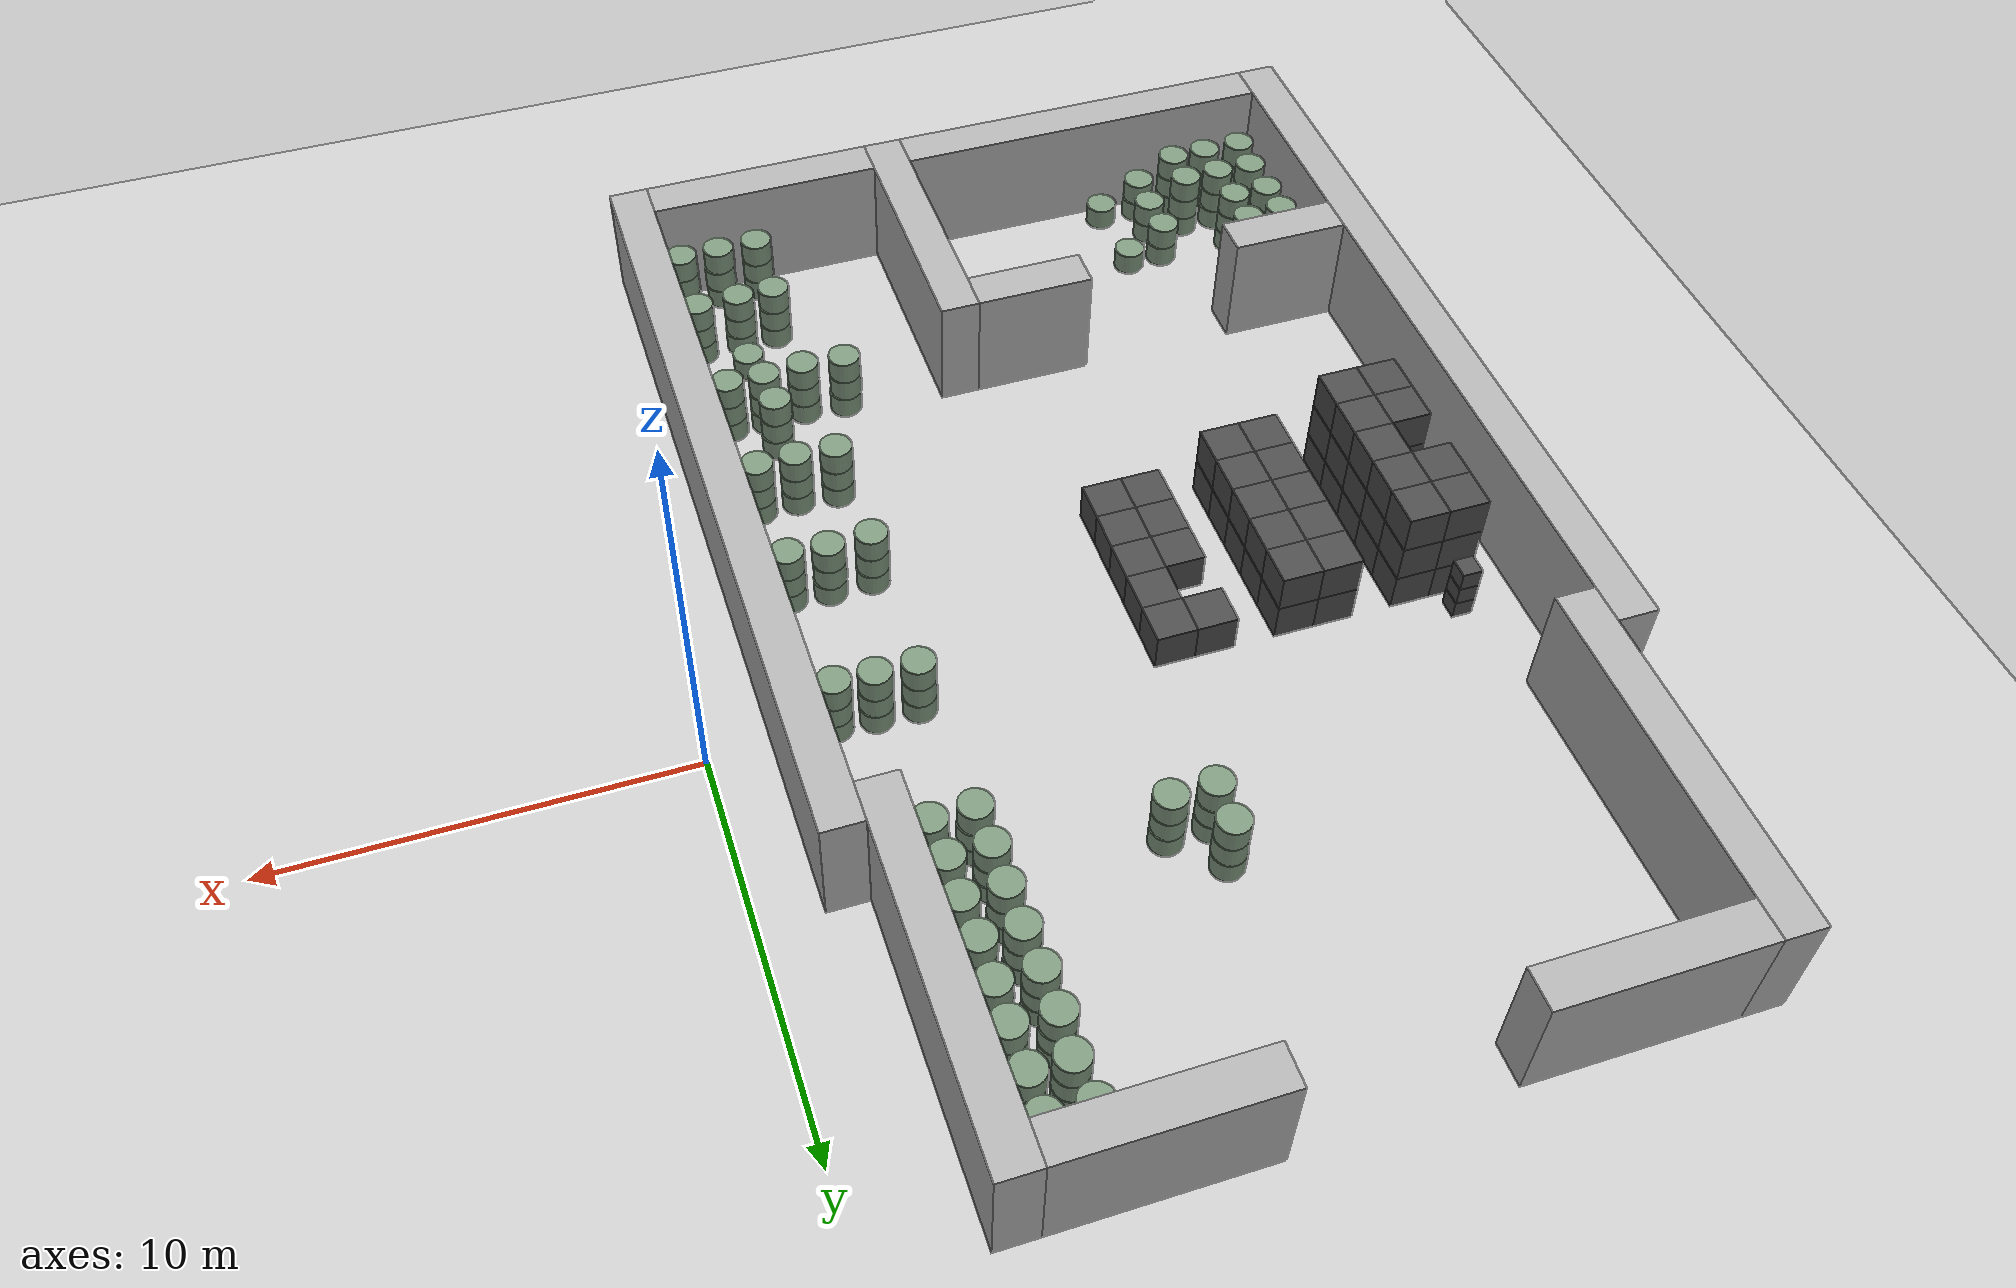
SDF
<sdf version="1.6">
 <world name="default">
  <light name="sun" type="directional">
   <cast_shadows>0</cast_shadows>
   <pose>0 0 10 0 -0 0</pose>
   <diffuse>0.8 0.8 0.8 1</diffuse>
   <specular>0.2 0.2 0.2 1</specular>
   <attenuation>
    <range>1000</range>
    <constant>0.9</constant>
    <linear>0.01</linear>
    <quadratic>0.001</quadratic>
   </attenuation>
   <direction>-0.5 0.1 -0.9</direction>
  </light>
  <include><uri>model://ground_plane</uri></include>
  <gravity>0 0 -9.8</gravity>
  <magnetic_field>6e-06 2.3e-05 -4.2e-05</magnetic_field>
  <atmosphere type="adiabatic"/>
  <physics name="default_physics" default="0" type="ode">
   <max_step_size>0.001</max_step_size>
   <real_time_factor>1</real_time_factor>
   <real_time_update_rate>1000</real_time_update_rate>
  </physics>
  <scene><ambient>0.4 0.4 0.4 1</ambient><background>0.7 0.7 0.7 1</background><shadows>0</shadows></scene>
  <spherical_coordinates>
   <surface_model>EARTH_WGS84</surface_model>
   <latitude_deg>0</latitude_deg>
   <longitude_deg>0</longitude_deg>
   <elevation>0</elevation>
   <heading_deg>0</heading_deg>
  </spherical_coordinates>
  <model name="wall_0">
   <pose>-20.0 -6.0 1.5 0 -0 0</pose>
   <static>True</static>
   <link name="link">
    <inertial>
     <mass>100</mass>
     <inertia>
      <ixx>0.166667</ixx>
      <ixy>0</ixy>
      <ixz>0</ixz>
      <iyy>0.166667</iyy>
      <iyz>0</iyz>
      <izz>0.166667</izz>
     </inertia>
    </inertial>
    <collision name="collision"><geometry><box><size>1.0 21.0 3.0</size></box></geometry></collision>
    <visual name="visual">
     <geometry><box><size>1.0 21.0 3.0</size></box></geometry>
     <material><ambient>0.7 0.7 0.7 1</ambient><diffuse>0.7 0.7 0.7 1</diffuse></material>
    </visual>
   </link>
  </model>
  <model name="wall_1">
   <pose>-19.0 8.0 1.5 0 -0 0</pose>
   <static>True</static>
   <link name="link">
    <inertial>
     <mass>100</mass>
     <inertia>
      <ixx>0.166667</ixx>
      <ixy>0</ixy>
      <ixz>0</ixz>
      <iyy>0.166667</iyy>
      <iyz>0</iyz>
      <izz>0.166667</izz>
     </inertia>
    </inertial>
    <collision name="collision"><geometry><box><size>1.0 9.0 3.0</size></box></geometry></collision>
    <visual name="visual">
     <geometry><box><size>1.0 9.0 3.0</size></box></geometry>
     <material><ambient>0.7 0.7 0.7 1</ambient><diffuse>0.7 0.7 0.7 1</diffuse></material>
    </visual>
   </link>
  </model>
  <model name="wall_2">
   <pose>-9.0 -13.0 1.5 0 -0 0</pose>
   <static>True</static>
   <link name="link">
    <inertial>
     <mass>100</mass>
     <inertia>
      <ixx>0.166667</ixx>
      <ixy>0</ixy>
      <ixz>0</ixz>
      <iyy>0.166667</iyy>
      <iyz>0</iyz>
      <izz>0.166667</izz>
     </inertia>
    </inertial>
    <collision name="collision"><geometry><box><size>1.0 7.0 3.0</size></box></geometry></collision>
    <visual name="visual">
     <geometry><box><size>1.0 7.0 3.0</size></box></geometry>
     <material><ambient>0.7 0.7 0.7 1</ambient><diffuse>0.7 0.7 0.7 1</diffuse></material>
    </visual>
   </link>
  </model>
  <model name="wall_3">
   <pose>-3.0 8.0 1.5 0 -0 0</pose>
   <static>True</static>
   <link name="link">
    <inertial>
     <mass>100</mass>
     <inertia>
      <ixx>0.166667</ixx>
      <ixy>0</ixy>
      <ixz>0</ixz>
      <iyy>0.166667</iyy>
      <iyz>0</iyz>
      <izz>0.166667</izz>
     </inertia>
    </inertial>
    <collision name="collision"><geometry><box><size>1.0 9.0 3.0</size></box></geometry></collision>
    <visual name="visual">
     <geometry><box><size>1.0 9.0 3.0</size></box></geometry>
     <material><ambient>0.7 0.7 0.7 1</ambient><diffuse>0.7 0.7 0.7 1</diffuse></material>
    </visual>
   </link>
  </model>
  <model name="wall_4">
   <pose>-2.0 -6.0 1.5 0 -0 0</pose>
   <static>True</static>
   <link name="link">
    <inertial>
     <mass>100</mass>
     <inertia>
      <ixx>0.166667</ixx>
      <ixy>0</ixy>
      <ixz>0</ixz>
      <iyy>0.166667</iyy>
      <iyz>0</iyz>
      <izz>0.166667</izz>
     </inertia>
    </inertial>
    <collision name="collision"><geometry><box><size>1.0 21.0 3.0</size></box></geometry></collision>
    <visual name="visual">
     <geometry><box><size>1.0 21.0 3.0</size></box></geometry>
     <material><ambient>0.7 0.7 0.7 1</ambient><diffuse>0.7 0.7 0.7 1</diffuse></material>
    </visual>
   </link>
  </model>
  <model name="wall_5">
   <pose>-14.5 -16.0 1.5 0 -0 0</pose>
   <static>True</static>
   <link name="link">
    <inertial>
     <mass>100</mass>
     <inertia>
      <ixx>0.166667</ixx>
      <ixy>0</ixy>
      <ixz>0</ixz>
      <iyy>0.166667</iyy>
      <iyz>0</iyz>
      <izz>0.166667</izz>
     </inertia>
    </inertial>
    <collision name="collision"><geometry><box><size>10.0 1.0 3.0</size></box></geometry></collision>
    <visual name="visual">
     <geometry><box><size>10.0 1.0 3.0</size></box></geometry>
     <material><ambient>0.7 0.7 0.7 1</ambient><diffuse>0.7 0.7 0.7 1</diffuse></material>
    </visual>
   </link>
  </model>
  <model name="wall_6">
   <pose>-5.5 -16.0 1.5 0 -0 0</pose>
   <static>True</static>
   <link name="link">
    <inertial>
     <mass>100</mass>
     <inertia>
      <ixx>0.166667</ixx>
      <ixy>0</ixy>
      <ixz>0</ixz>
      <iyy>0.166667</iyy>
      <iyz>0</iyz>
      <izz>0.166667</izz>
     </inertia>
    </inertial>
    <collision name="collision"><geometry><box><size>6.0 1.0 3.0</size></box></geometry></collision>
    <visual name="visual">
     <geometry><box><size>6.0 1.0 3.0</size></box></geometry>
     <material><ambient>0.7 0.7 0.7 1</ambient><diffuse>0.7 0.7 0.7 1</diffuse></material>
    </visual>
   </link>
  </model>
  <model name="wall_7">
   <pose>-18.0 -10.0 1.5 0 -0 0</pose>
   <static>True</static>
   <link name="link">
    <inertial>
     <mass>100</mass>
     <inertia>
      <ixx>0.166667</ixx>
      <ixy>0</ixy>
      <ixz>0</ixz>
      <iyy>0.166667</iyy>
      <iyz>0</iyz>
      <izz>0.166667</izz>
     </inertia>
    </inertial>
    <collision name="collision"><geometry><box><size>3.0 1.0 3.0</size></box></geometry></collision>
    <visual name="visual">
     <geometry><box><size>3.0 1.0 3.0</size></box></geometry>
     <material><ambient>0.7 0.7 0.7 1</ambient><diffuse>0.7 0.7 0.7 1</diffuse></material>
    </visual>
   </link>
  </model>
  <model name="wall_8">
   <pose>-11.0 -10.0 1.5 0 -0 0</pose>
   <static>True</static>
   <link name="link">
    <inertial>
     <mass>100</mass>
     <inertia>
      <ixx>0.166667</ixx>
      <ixy>0</ixy>
      <ixz>0</ixz>
      <iyy>0.166667</iyy>
      <iyz>0</iyz>
      <izz>0.166667</izz>
     </inertia>
    </inertial>
    <collision name="collision"><geometry><box><size>3.0 1.0 3.0</size></box></geometry></collision>
    <visual name="visual">
     <geometry><box><size>3.0 1.0 3.0</size></box></geometry>
     <material><ambient>0.7 0.7 0.7 1</ambient><diffuse>0.7 0.7 0.7 1</diffuse></material>
    </visual>
   </link>
  </model>
  <model name="wall_9">
   <pose>-16.0 12.0 1.5 0 -0 0</pose>
   <static>True</static>
   <link name="link">
    <inertial>
     <mass>100</mass>
     <inertia>
      <ixx>0.166667</ixx>
      <ixy>0</ixy>
      <ixz>0</ixz>
      <iyy>0.166667</iyy>
      <iyz>0</iyz>
      <izz>0.166667</izz>
     </inertia>
    </inertial>
    <collision name="collision"><geometry><box><size>5.0 1.0 3.0</size></box></geometry></collision>
    <visual name="visual">
     <geometry><box><size>5.0 1.0 3.0</size></box></geometry>
     <material><ambient>0.7 0.7 0.7 1</ambient><diffuse>0.7 0.7 0.7 1</diffuse></material>
    </visual>
   </link>
  </model>
  <model name="wall_10">
   <pose>-6.0 12.0 1.5 0 -0 0</pose>
   <static>True</static>
   <link name="link">
    <inertial>
     <mass>100</mass>
     <inertia>
      <ixx>0.166667</ixx>
      <ixy>0</ixy>
      <ixz>0</ixz>
      <iyy>0.166667</iyy>
      <iyz>0</iyz>
      <izz>0.166667</izz>
     </inertia>
    </inertial>
    <collision name="collision"><geometry><box><size>5.0 1.0 3.0</size></box></geometry></collision>
    <visual name="visual">
     <geometry><box><size>5.0 1.0 3.0</size></box></geometry>
     <material><ambient>0.7 0.7 0.7 1</ambient><diffuse>0.7 0.7 0.7 1</diffuse></material>
    </visual>
   </link>
  </model>
  <model name="unit_box_0">
   <pose>-18.0 -4.0 0.5 0 -0 0</pose>
   <static>True</static>
   <link name="link">
    <inertial>
     <mass>100</mass>
     <inertia>
      <ixx>0.166667</ixx>
      <ixy>0</ixy>
      <ixz>0</ixz>
      <iyy>0.166667</iyy>
      <iyz>0</iyz>
      <izz>0.166667</izz>
     </inertia>
    </inertial>
    <collision name="collision"><geometry><box><size>1.0 1.0 1.0</size></box></geometry></collision>
    <visual name="visual">
     <geometry><box><size>1.0 1.0 1.0</size></box></geometry>
     <material><ambient>0.3 0.3 0.3 1</ambient><diffuse>0.3 0.3 0.3 1</diffuse></material>
    </visual>
   </link>
  </model>
  <model name="unit_box_1">
   <pose>-18.0 -4.0 1.5 0 -0 0</pose>
   <static>True</static>
   <link name="link">
    <inertial>
     <mass>100</mass>
     <inertia>
      <ixx>0.166667</ixx>
      <ixy>0</ixy>
      <ixz>0</ixz>
      <iyy>0.166667</iyy>
      <iyz>0</iyz>
      <izz>0.166667</izz>
     </inertia>
    </inertial>
    <collision name="collision"><geometry><box><size>1.0 1.0 1.0</size></box></geometry></collision>
    <visual name="visual">
     <geometry><box><size>1.0 1.0 1.0</size></box></geometry>
     <material><ambient>0.3 0.3 0.3 1</ambient><diffuse>0.3 0.3 0.3 1</diffuse></material>
    </visual>
   </link>
  </model>
  <model name="unit_box_2">
   <pose>-18.0 -4.0 2.5 0 -0 0</pose>
   <static>True</static>
   <link name="link">
    <inertial>
     <mass>100</mass>
     <inertia>
      <ixx>0.166667</ixx>
      <ixy>0</ixy>
      <ixz>0</ixz>
      <iyy>0.166667</iyy>
      <iyz>0</iyz>
      <izz>0.166667</izz>
     </inertia>
    </inertial>
    <collision name="collision"><geometry><box><size>1.0 1.0 1.0</size></box></geometry></collision>
    <visual name="visual">
     <geometry><box><size>1.0 1.0 1.0</size></box></geometry>
     <material><ambient>0.3 0.3 0.3 1</ambient><diffuse>0.3 0.3 0.3 1</diffuse></material>
    </visual>
   </link>
  </model>
  <model name="unit_box_3">
   <pose>-18.0 -3.0 0.5 0 -0 0</pose>
   <static>True</static>
   <link name="link">
    <inertial>
     <mass>100</mass>
     <inertia>
      <ixx>0.166667</ixx>
      <ixy>0</ixy>
      <ixz>0</ixz>
      <iyy>0.166667</iyy>
      <iyz>0</iyz>
      <izz>0.166667</izz>
     </inertia>
    </inertial>
    <collision name="collision"><geometry><box><size>1.0 1.0 1.0</size></box></geometry></collision>
    <visual name="visual">
     <geometry><box><size>1.0 1.0 1.0</size></box></geometry>
     <material><ambient>0.3 0.3 0.3 1</ambient><diffuse>0.3 0.3 0.3 1</diffuse></material>
    </visual>
   </link>
  </model>
  <model name="unit_box_4">
   <pose>-18.0 -3.0 1.5 0 -0 0</pose>
   <static>True</static>
   <link name="link">
    <inertial>
     <mass>100</mass>
     <inertia>
      <ixx>0.166667</ixx>
      <ixy>0</ixy>
      <ixz>0</ixz>
      <iyy>0.166667</iyy>
      <iyz>0</iyz>
      <izz>0.166667</izz>
     </inertia>
    </inertial>
    <collision name="collision"><geometry><box><size>1.0 1.0 1.0</size></box></geometry></collision>
    <visual name="visual">
     <geometry><box><size>1.0 1.0 1.0</size></box></geometry>
     <material><ambient>0.3 0.3 0.3 1</ambient><diffuse>0.3 0.3 0.3 1</diffuse></material>
    </visual>
   </link>
  </model>
  <model name="unit_box_5">
   <pose>-18.0 -3.0 2.5 0 -0 0</pose>
   <static>True</static>
   <link name="link">
    <inertial>
     <mass>100</mass>
     <inertia>
      <ixx>0.166667</ixx>
      <ixy>0</ixy>
      <ixz>0</ixz>
      <iyy>0.166667</iyy>
      <iyz>0</iyz>
      <izz>0.166667</izz>
     </inertia>
    </inertial>
    <collision name="collision"><geometry><box><size>1.0 1.0 1.0</size></box></geometry></collision>
    <visual name="visual">
     <geometry><box><size>1.0 1.0 1.0</size></box></geometry>
     <material><ambient>0.3 0.3 0.3 1</ambient><diffuse>0.3 0.3 0.3 1</diffuse></material>
    </visual>
   </link>
  </model>
  <model name="unit_box_6">
   <pose>-18.0 -1.0 0.5 0 -0 0</pose>
   <static>True</static>
   <link name="link">
    <inertial>
     <mass>100</mass>
     <inertia>
      <ixx>0.166667</ixx>
      <ixy>0</ixy>
      <ixz>0</ixz>
      <iyy>0.166667</iyy>
      <iyz>0</iyz>
      <izz>0.166667</izz>
     </inertia>
    </inertial>
    <collision name="collision"><geometry><box><size>1.0 1.0 1.0</size></box></geometry></collision>
    <visual name="visual">
     <geometry><box><size>1.0 1.0 1.0</size></box></geometry>
     <material><ambient>0.3 0.3 0.3 1</ambient><diffuse>0.3 0.3 0.3 1</diffuse></material>
    </visual>
   </link>
  </model>
  <model name="unit_box_7">
   <pose>-18.0 -1.0 1.5 0 -0 0</pose>
   <static>True</static>
   <link name="link">
    <inertial>
     <mass>100</mass>
     <inertia>
      <ixx>0.166667</ixx>
      <ixy>0</ixy>
      <ixz>0</ixz>
      <iyy>0.166667</iyy>
      <iyz>0</iyz>
      <izz>0.166667</izz>
     </inertia>
    </inertial>
    <collision name="collision"><geometry><box><size>1.0 1.0 1.0</size></box></geometry></collision>
    <visual name="visual">
     <geometry><box><size>1.0 1.0 1.0</size></box></geometry>
     <material><ambient>0.3 0.3 0.3 1</ambient><diffuse>0.3 0.3 0.3 1</diffuse></material>
    </visual>
   </link>
  </model>
  <model name="unit_box_8">
   <pose>-18.0 -1.0 2.5 0 -0 0</pose>
   <static>True</static>
   <link name="link">
    <inertial>
     <mass>100</mass>
     <inertia>
      <ixx>0.166667</ixx>
      <ixy>0</ixy>
      <ixz>0</ixz>
      <iyy>0.166667</iyy>
      <iyz>0</iyz>
      <izz>0.166667</izz>
     </inertia>
    </inertial>
    <collision name="collision"><geometry><box><size>1.0 1.0 1.0</size></box></geometry></collision>
    <visual name="visual">
     <geometry><box><size>1.0 1.0 1.0</size></box></geometry>
     <material><ambient>0.3 0.3 0.3 1</ambient><diffuse>0.3 0.3 0.3 1</diffuse></material>
    </visual>
   </link>
  </model>
  <model name="unit_box_9">
   <pose>-18.0 0.0 0.5 0 -0 0</pose>
   <static>True</static>
   <link name="link">
    <inertial>
     <mass>100</mass>
     <inertia>
      <ixx>0.166667</ixx>
      <ixy>0</ixy>
      <ixz>0</ixz>
      <iyy>0.166667</iyy>
      <iyz>0</iyz>
      <izz>0.166667</izz>
     </inertia>
    </inertial>
    <collision name="collision"><geometry><box><size>1.0 1.0 1.0</size></box></geometry></collision>
    <visual name="visual">
     <geometry><box><size>1.0 1.0 1.0</size></box></geometry>
     <material><ambient>0.3 0.3 0.3 1</ambient><diffuse>0.3 0.3 0.3 1</diffuse></material>
    </visual>
   </link>
  </model>
  <model name="unit_box_10">
   <pose>-18.0 0.0 1.5 0 -0 0</pose>
   <static>True</static>
   <link name="link">
    <inertial>
     <mass>100</mass>
     <inertia>
      <ixx>0.166667</ixx>
      <ixy>0</ixy>
      <ixz>0</ixz>
      <iyy>0.166667</iyy>
      <iyz>0</iyz>
      <izz>0.166667</izz>
     </inertia>
    </inertial>
    <collision name="collision"><geometry><box><size>1.0 1.0 1.0</size></box></geometry></collision>
    <visual name="visual">
     <geometry><box><size>1.0 1.0 1.0</size></box></geometry>
     <material><ambient>0.3 0.3 0.3 1</ambient><diffuse>0.3 0.3 0.3 1</diffuse></material>
    </visual>
   </link>
  </model>
  <model name="unit_box_11">
   <pose>-18.0 0.0 2.5 0 -0 0</pose>
   <static>True</static>
   <link name="link">
    <inertial>
     <mass>100</mass>
     <inertia>
      <ixx>0.166667</ixx>
      <ixy>0</ixy>
      <ixz>0</ixz>
      <iyy>0.166667</iyy>
      <iyz>0</iyz>
      <izz>0.166667</izz>
     </inertia>
    </inertial>
    <collision name="collision"><geometry><box><size>1.0 1.0 1.0</size></box></geometry></collision>
    <visual name="visual">
     <geometry><box><size>1.0 1.0 1.0</size></box></geometry>
     <material><ambient>0.3 0.3 0.3 1</ambient><diffuse>0.3 0.3 0.3 1</diffuse></material>
    </visual>
   </link>
  </model>
  <model name="unit_box_12">
   <pose>-18.0 1.0 0.25 0 -0 0</pose>
   <static>True</static>
   <link name="link">
    <inertial>
     <mass>100</mass>
     <inertia>
      <ixx>0.166667</ixx>
      <ixy>0</ixy>
      <ixz>0</ixz>
      <iyy>0.166667</iyy>
      <iyz>0</iyz>
      <izz>0.166667</izz>
     </inertia>
    </inertial>
    <collision name="collision"><geometry><box><size>0.5 0.5 0.5</size></box></geometry></collision>
    <visual name="visual">
     <geometry><box><size>0.5 0.5 0.5</size></box></geometry>
     <material><ambient>0.3 0.3 0.3 1</ambient><diffuse>0.3 0.3 0.3 1</diffuse></material>
    </visual>
   </link>
  </model>
  <model name="unit_box_13">
   <pose>-18.0 1.0 0.75 0 -0 0</pose>
   <static>True</static>
   <link name="link">
    <inertial>
     <mass>100</mass>
     <inertia>
      <ixx>0.166667</ixx>
      <ixy>0</ixy>
      <ixz>0</ixz>
      <iyy>0.166667</iyy>
      <iyz>0</iyz>
      <izz>0.166667</izz>
     </inertia>
    </inertial>
    <collision name="collision"><geometry><box><size>0.5 0.5 0.5</size></box></geometry></collision>
    <visual name="visual">
     <geometry><box><size>0.5 0.5 0.5</size></box></geometry>
     <material><ambient>0.3 0.3 0.3 1</ambient><diffuse>0.3 0.3 0.3 1</diffuse></material>
    </visual>
   </link>
  </model>
  <model name="unit_box_14">
   <pose>-18.0 1.0 1.25 0 -0 0</pose>
   <static>True</static>
   <link name="link">
    <inertial>
     <mass>100</mass>
     <inertia>
      <ixx>0.166667</ixx>
      <ixy>0</ixy>
      <ixz>0</ixz>
      <iyy>0.166667</iyy>
      <iyz>0</iyz>
      <izz>0.166667</izz>
     </inertia>
    </inertial>
    <collision name="collision"><geometry><box><size>0.5 0.5 0.5</size></box></geometry></collision>
    <visual name="visual">
     <geometry><box><size>0.5 0.5 0.5</size></box></geometry>
     <material><ambient>0.3 0.3 0.3 1</ambient><diffuse>0.3 0.3 0.3 1</diffuse></material>
    </visual>
   </link>
  </model>
  <model name="unit_box_15">
   <pose>-17.0 -4.0 0.5 0 -0 0</pose>
   <static>True</static>
   <link name="link">
    <inertial>
     <mass>100</mass>
     <inertia>
      <ixx>0.166667</ixx>
      <ixy>0</ixy>
      <ixz>0</ixz>
      <iyy>0.166667</iyy>
      <iyz>0</iyz>
      <izz>0.166667</izz>
     </inertia>
    </inertial>
    <collision name="collision"><geometry><box><size>1.0 1.0 1.0</size></box></geometry></collision>
    <visual name="visual">
     <geometry><box><size>1.0 1.0 1.0</size></box></geometry>
     <material><ambient>0.3 0.3 0.3 1</ambient><diffuse>0.3 0.3 0.3 1</diffuse></material>
    </visual>
   </link>
  </model>
  <model name="unit_box_16">
   <pose>-17.0 -4.0 1.5 0 -0 0</pose>
   <static>True</static>
   <link name="link">
    <inertial>
     <mass>100</mass>
     <inertia>
      <ixx>0.166667</ixx>
      <ixy>0</ixy>
      <ixz>0</ixz>
      <iyy>0.166667</iyy>
      <iyz>0</iyz>
      <izz>0.166667</izz>
     </inertia>
    </inertial>
    <collision name="collision"><geometry><box><size>1.0 1.0 1.0</size></box></geometry></collision>
    <visual name="visual">
     <geometry><box><size>1.0 1.0 1.0</size></box></geometry>
     <material><ambient>0.3 0.3 0.3 1</ambient><diffuse>0.3 0.3 0.3 1</diffuse></material>
    </visual>
   </link>
  </model>
  <model name="unit_box_17">
   <pose>-17.0 -4.0 2.5 0 -0 0</pose>
   <static>True</static>
   <link name="link">
    <inertial>
     <mass>100</mass>
     <inertia>
      <ixx>0.166667</ixx>
      <ixy>0</ixy>
      <ixz>0</ixz>
      <iyy>0.166667</iyy>
      <iyz>0</iyz>
      <izz>0.166667</izz>
     </inertia>
    </inertial>
    <collision name="collision"><geometry><box><size>1.0 1.0 1.0</size></box></geometry></collision>
    <visual name="visual">
     <geometry><box><size>1.0 1.0 1.0</size></box></geometry>
     <material><ambient>0.3 0.3 0.3 1</ambient><diffuse>0.3 0.3 0.3 1</diffuse></material>
    </visual>
   </link>
  </model>
  <model name="unit_box_18">
   <pose>-17.0 -3.0 0.5 0 -0 0</pose>
   <static>True</static>
   <link name="link">
    <inertial>
     <mass>100</mass>
     <inertia>
      <ixx>0.166667</ixx>
      <ixy>0</ixy>
      <ixz>0</ixz>
      <iyy>0.166667</iyy>
      <iyz>0</iyz>
      <izz>0.166667</izz>
     </inertia>
    </inertial>
    <collision name="collision"><geometry><box><size>1.0 1.0 1.0</size></box></geometry></collision>
    <visual name="visual">
     <geometry><box><size>1.0 1.0 1.0</size></box></geometry>
     <material><ambient>0.3 0.3 0.3 1</ambient><diffuse>0.3 0.3 0.3 1</diffuse></material>
    </visual>
   </link>
  </model>
  <model name="unit_box_19">
   <pose>-17.0 -3.0 1.5 0 -0 0</pose>
   <static>True</static>
   <link name="link">
    <inertial>
     <mass>100</mass>
     <inertia>
      <ixx>0.166667</ixx>
      <ixy>0</ixy>
      <ixz>0</ixz>
      <iyy>0.166667</iyy>
      <iyz>0</iyz>
      <izz>0.166667</izz>
     </inertia>
    </inertial>
    <collision name="collision"><geometry><box><size>1.0 1.0 1.0</size></box></geometry></collision>
    <visual name="visual">
     <geometry><box><size>1.0 1.0 1.0</size></box></geometry>
     <material><ambient>0.3 0.3 0.3 1</ambient><diffuse>0.3 0.3 0.3 1</diffuse></material>
    </visual>
   </link>
  </model>
  <model name="unit_box_20">
   <pose>-17.0 -3.0 2.5 0 -0 0</pose>
   <static>True</static>
   <link name="link">
    <inertial>
     <mass>100</mass>
     <inertia>
      <ixx>0.166667</ixx>
      <ixy>0</ixy>
      <ixz>0</ixz>
      <iyy>0.166667</iyy>
      <iyz>0</iyz>
      <izz>0.166667</izz>
     </inertia>
    </inertial>
    <collision name="collision"><geometry><box><size>1.0 1.0 1.0</size></box></geometry></collision>
    <visual name="visual">
     <geometry><box><size>1.0 1.0 1.0</size></box></geometry>
     <material><ambient>0.3 0.3 0.3 1</ambient><diffuse>0.3 0.3 0.3 1</diffuse></material>
    </visual>
   </link>
  </model>
  <model name="unit_box_21">
   <pose>-17.0 -2.0 0.5 0 -0 0</pose>
   <static>True</static>
   <link name="link">
    <inertial>
     <mass>100</mass>
     <inertia>
      <ixx>0.166667</ixx>
      <ixy>0</ixy>
      <ixz>0</ixz>
      <iyy>0.166667</iyy>
      <iyz>0</iyz>
      <izz>0.166667</izz>
     </inertia>
    </inertial>
    <collision name="collision"><geometry><box><size>1.0 1.0 1.0</size></box></geometry></collision>
    <visual name="visual">
     <geometry><box><size>1.0 1.0 1.0</size></box></geometry>
     <material><ambient>0.3 0.3 0.3 1</ambient><diffuse>0.3 0.3 0.3 1</diffuse></material>
    </visual>
   </link>
  </model>
  <model name="unit_box_22">
   <pose>-17.0 -2.0 1.5 0 -0 0</pose>
   <static>True</static>
   <link name="link">
    <inertial>
     <mass>100</mass>
     <inertia>
      <ixx>0.166667</ixx>
      <ixy>0</ixy>
      <ixz>0</ixz>
      <iyy>0.166667</iyy>
      <iyz>0</iyz>
      <izz>0.166667</izz>
     </inertia>
    </inertial>
    <collision name="collision"><geometry><box><size>1.0 1.0 1.0</size></box></geometry></collision>
    <visual name="visual">
     <geometry><box><size>1.0 1.0 1.0</size></box></geometry>
     <material><ambient>0.3 0.3 0.3 1</ambient><diffuse>0.3 0.3 0.3 1</diffuse></material>
    </visual>
   </link>
  </model>
  <model name="unit_box_23">
   <pose>-17.0 -2.0 2.5 0 -0 0</pose>
   <static>True</static>
   <link name="link">
    <inertial>
     <mass>100</mass>
     <inertia>
      <ixx>0.166667</ixx>
      <ixy>0</ixy>
      <ixz>0</ixz>
      <iyy>0.166667</iyy>
      <iyz>0</iyz>
      <izz>0.166667</izz>
     </inertia>
    </inertial>
    <collision name="collision"><geometry><box><size>1.0 1.0 1.0</size></box></geometry></collision>
    <visual name="visual">
     <geometry><box><size>1.0 1.0 1.0</size></box></geometry>
     <material><ambient>0.3 0.3 0.3 1</ambient><diffuse>0.3 0.3 0.3 1</diffuse></material>
    </visual>
   </link>
  </model>
  <model name="unit_box_24">
   <pose>-17.0 -1.0 0.5 0 -0 0</pose>
   <static>True</static>
   <link name="link">
    <inertial>
     <mass>100</mass>
     <inertia>
      <ixx>0.166667</ixx>
      <ixy>0</ixy>
      <ixz>0</ixz>
      <iyy>0.166667</iyy>
      <iyz>0</iyz>
      <izz>0.166667</izz>
     </inertia>
    </inertial>
    <collision name="collision"><geometry><box><size>1.0 1.0 1.0</size></box></geometry></collision>
    <visual name="visual">
     <geometry><box><size>1.0 1.0 1.0</size></box></geometry>
     <material><ambient>0.3 0.3 0.3 1</ambient><diffuse>0.3 0.3 0.3 1</diffuse></material>
    </visual>
   </link>
  </model>
  <model name="unit_box_25">
   <pose>-17.0 -1.0 1.5 0 -0 0</pose>
   <static>True</static>
   <link name="link">
    <inertial>
     <mass>100</mass>
     <inertia>
      <ixx>0.166667</ixx>
      <ixy>0</ixy>
      <ixz>0</ixz>
      <iyy>0.166667</iyy>
      <iyz>0</iyz>
      <izz>0.166667</izz>
     </inertia>
    </inertial>
    <collision name="collision"><geometry><box><size>1.0 1.0 1.0</size></box></geometry></collision>
    <visual name="visual">
     <geometry><box><size>1.0 1.0 1.0</size></box></geometry>
     <material><ambient>0.3 0.3 0.3 1</ambient><diffuse>0.3 0.3 0.3 1</diffuse></material>
    </visual>
   </link>
  </model>
  <model name="unit_box_26">
   <pose>-17.0 -1.0 2.5 0 -0 0</pose>
   <static>True</static>
   <link name="link">
    <inertial>
     <mass>100</mass>
     <inertia>
      <ixx>0.166667</ixx>
      <ixy>0</ixy>
      <ixz>0</ixz>
      <iyy>0.166667</iyy>
      <iyz>0</iyz>
      <izz>0.166667</izz>
     </inertia>
    </inertial>
    <collision name="collision"><geometry><box><size>1.0 1.0 1.0</size></box></geometry></collision>
    <visual name="visual">
     <geometry><box><size>1.0 1.0 1.0</size></box></geometry>
     <material><ambient>0.3 0.3 0.3 1</ambient><diffuse>0.3 0.3 0.3 1</diffuse></material>
    </visual>
   </link>
  </model>
  <model name="unit_box_27">
   <pose>-17.0 0.0 0.5 0 -0 0</pose>
   <static>True</static>
   <link name="link">
    <inertial>
     <mass>100</mass>
     <inertia>
      <ixx>0.166667</ixx>
      <ixy>0</ixy>
      <ixz>0</ixz>
      <iyy>0.166667</iyy>
      <iyz>0</iyz>
      <izz>0.166667</izz>
     </inertia>
    </inertial>
    <collision name="collision"><geometry><box><size>1.0 1.0 1.0</size></box></geometry></collision>
    <visual name="visual">
     <geometry><box><size>1.0 1.0 1.0</size></box></geometry>
     <material><ambient>0.3 0.3 0.3 1</ambient><diffuse>0.3 0.3 0.3 1</diffuse></material>
    </visual>
   </link>
  </model>
  <model name="unit_box_28">
   <pose>-17.0 0.0 1.5 0 -0 0</pose>
   <static>True</static>
   <link name="link">
    <inertial>
     <mass>100</mass>
     <inertia>
      <ixx>0.166667</ixx>
      <ixy>0</ixy>
      <ixz>0</ixz>
      <iyy>0.166667</iyy>
      <iyz>0</iyz>
      <izz>0.166667</izz>
     </inertia>
    </inertial>
    <collision name="collision"><geometry><box><size>1.0 1.0 1.0</size></box></geometry></collision>
    <visual name="visual">
     <geometry><box><size>1.0 1.0 1.0</size></box></geometry>
     <material><ambient>0.3 0.3 0.3 1</ambient><diffuse>0.3 0.3 0.3 1</diffuse></material>
    </visual>
   </link>
  </model>
  <model name="unit_box_29">
   <pose>-17.0 0.0 2.5 0 -0 0</pose>
   <static>True</static>
   <link name="link">
    <inertial>
     <mass>100</mass>
     <inertia>
      <ixx>0.166667</ixx>
      <ixy>0</ixy>
      <ixz>0</ixz>
      <iyy>0.166667</iyy>
      <iyz>0</iyz>
      <izz>0.166667</izz>
     </inertia>
    </inertial>
    <collision name="collision"><geometry><box><size>1.0 1.0 1.0</size></box></geometry></collision>
    <visual name="visual">
     <geometry><box><size>1.0 1.0 1.0</size></box></geometry>
     <material><ambient>0.3 0.3 0.3 1</ambient><diffuse>0.3 0.3 0.3 1</diffuse></material>
    </visual>
   </link>
  </model>
  <model name="unit_box_30">
   <pose>-16.0 -1.0 0.25 0 -0 0</pose>
   <static>True</static>
   <link name="link">
    <inertial>
     <mass>100</mass>
     <inertia>
      <ixx>0.166667</ixx>
      <ixy>0</ixy>
      <ixz>0</ixz>
      <iyy>0.166667</iyy>
      <iyz>0</iyz>
      <izz>0.166667</izz>
     </inertia>
    </inertial>
    <collision name="collision"><geometry><box><size>0.5 0.5 0.5</size></box></geometry></collision>
    <visual name="visual">
     <geometry><box><size>0.5 0.5 0.5</size></box></geometry>
     <material><ambient>0.3 0.3 0.3 1</ambient><diffuse>0.3 0.3 0.3 1</diffuse></material>
    </visual>
   </link>
  </model>
  <model name="unit_box_31">
   <pose>-15.0 -4.0 0.5 0 -0 0</pose>
   <static>True</static>
   <link name="link">
    <inertial>
     <mass>100</mass>
     <inertia>
      <ixx>0.166667</ixx>
      <ixy>0</ixy>
      <ixz>0</ixz>
      <iyy>0.166667</iyy>
      <iyz>0</iyz>
      <izz>0.166667</izz>
     </inertia>
    </inertial>
    <collision name="collision"><geometry><box><size>1.0 1.0 1.0</size></box></geometry></collision>
    <visual name="visual">
     <geometry><box><size>1.0 1.0 1.0</size></box></geometry>
     <material><ambient>0.3 0.3 0.3 1</ambient><diffuse>0.3 0.3 0.3 1</diffuse></material>
    </visual>
   </link>
  </model>
  <model name="unit_box_32">
   <pose>-15.0 -4.0 1.5 0 -0 0</pose>
   <static>True</static>
   <link name="link">
    <inertial>
     <mass>100</mass>
     <inertia>
      <ixx>0.166667</ixx>
      <ixy>0</ixy>
      <ixz>0</ixz>
      <iyy>0.166667</iyy>
      <iyz>0</iyz>
      <izz>0.166667</izz>
     </inertia>
    </inertial>
    <collision name="collision"><geometry><box><size>1.0 1.0 1.0</size></box></geometry></collision>
    <visual name="visual">
     <geometry><box><size>1.0 1.0 1.0</size></box></geometry>
     <material><ambient>0.3 0.3 0.3 1</ambient><diffuse>0.3 0.3 0.3 1</diffuse></material>
    </visual>
   </link>
  </model>
  <model name="unit_box_33">
   <pose>-15.0 -3.0 0.5 0 -0 0</pose>
   <static>True</static>
   <link name="link">
    <inertial>
     <mass>100</mass>
     <inertia>
      <ixx>0.166667</ixx>
      <ixy>0</ixy>
      <ixz>0</ixz>
      <iyy>0.166667</iyy>
      <iyz>0</iyz>
      <izz>0.166667</izz>
     </inertia>
    </inertial>
    <collision name="collision"><geometry><box><size>1.0 1.0 1.0</size></box></geometry></collision>
    <visual name="visual">
     <geometry><box><size>1.0 1.0 1.0</size></box></geometry>
     <material><ambient>0.3 0.3 0.3 1</ambient><diffuse>0.3 0.3 0.3 1</diffuse></material>
    </visual>
   </link>
  </model>
  <model name="unit_box_34">
   <pose>-15.0 -3.0 1.5 0 -0 0</pose>
   <static>True</static>
   <link name="link">
    <inertial>
     <mass>100</mass>
     <inertia>
      <ixx>0.166667</ixx>
      <ixy>0</ixy>
      <ixz>0</ixz>
      <iyy>0.166667</iyy>
      <iyz>0</iyz>
      <izz>0.166667</izz>
     </inertia>
    </inertial>
    <collision name="collision"><geometry><box><size>1.0 1.0 1.0</size></box></geometry></collision>
    <visual name="visual">
     <geometry><box><size>1.0 1.0 1.0</size></box></geometry>
     <material><ambient>0.3 0.3 0.3 1</ambient><diffuse>0.3 0.3 0.3 1</diffuse></material>
    </visual>
   </link>
  </model>
  <model name="unit_box_35">
   <pose>-15.0 -2.0 0.5 0 -0 0</pose>
   <static>True</static>
   <link name="link">
    <inertial>
     <mass>100</mass>
     <inertia>
      <ixx>0.166667</ixx>
      <ixy>0</ixy>
      <ixz>0</ixz>
      <iyy>0.166667</iyy>
      <iyz>0</iyz>
      <izz>0.166667</izz>
     </inertia>
    </inertial>
    <collision name="collision"><geometry><box><size>1.0 1.0 1.0</size></box></geometry></collision>
    <visual name="visual">
     <geometry><box><size>1.0 1.0 1.0</size></box></geometry>
     <material><ambient>0.3 0.3 0.3 1</ambient><diffuse>0.3 0.3 0.3 1</diffuse></material>
    </visual>
   </link>
  </model>
  <model name="unit_box_36">
   <pose>-15.0 -2.0 1.5 0 -0 0</pose>
   <static>True</static>
   <link name="link">
    <inertial>
     <mass>100</mass>
     <inertia>
      <ixx>0.166667</ixx>
      <ixy>0</ixy>
      <ixz>0</ixz>
      <iyy>0.166667</iyy>
      <iyz>0</iyz>
      <izz>0.166667</izz>
     </inertia>
    </inertial>
    <collision name="collision"><geometry><box><size>1.0 1.0 1.0</size></box></geometry></collision>
    <visual name="visual">
     <geometry><box><size>1.0 1.0 1.0</size></box></geometry>
     <material><ambient>0.3 0.3 0.3 1</ambient><diffuse>0.3 0.3 0.3 1</diffuse></material>
    </visual>
   </link>
  </model>
  <model name="unit_box_37">
   <pose>-15.0 -1.0 0.5 0 -0 0</pose>
   <static>True</static>
   <link name="link">
    <inertial>
     <mass>100</mass>
     <inertia>
      <ixx>0.166667</ixx>
      <ixy>0</ixy>
      <ixz>0</ixz>
      <iyy>0.166667</iyy>
      <iyz>0</iyz>
      <izz>0.166667</izz>
     </inertia>
    </inertial>
    <collision name="collision"><geometry><box><size>1.0 1.0 1.0</size></box></geometry></collision>
    <visual name="visual">
     <geometry><box><size>1.0 1.0 1.0</size></box></geometry>
     <material><ambient>0.3 0.3 0.3 1</ambient><diffuse>0.3 0.3 0.3 1</diffuse></material>
    </visual>
   </link>
  </model>
  <model name="unit_box_38">
   <pose>-15.0 -1.0 1.5 0 -0 0</pose>
   <static>True</static>
   <link name="link">
    <inertial>
     <mass>100</mass>
     <inertia>
      <ixx>0.166667</ixx>
      <ixy>0</ixy>
      <ixz>0</ixz>
      <iyy>0.166667</iyy>
      <iyz>0</iyz>
      <izz>0.166667</izz>
     </inertia>
    </inertial>
    <collision name="collision"><geometry><box><size>1.0 1.0 1.0</size></box></geometry></collision>
    <visual name="visual">
     <geometry><box><size>1.0 1.0 1.0</size></box></geometry>
     <material><ambient>0.3 0.3 0.3 1</ambient><diffuse>0.3 0.3 0.3 1</diffuse></material>
    </visual>
   </link>
  </model>
  <model name="unit_box_39">
   <pose>-15.0 0.0 0.5 0 -0 0</pose>
   <static>True</static>
   <link name="link">
    <inertial>
     <mass>100</mass>
     <inertia>
      <ixx>0.166667</ixx>
      <ixy>0</ixy>
      <ixz>0</ixz>
      <iyy>0.166667</iyy>
      <iyz>0</iyz>
      <izz>0.166667</izz>
     </inertia>
    </inertial>
    <collision name="collision"><geometry><box><size>1.0 1.0 1.0</size></box></geometry></collision>
    <visual name="visual">
     <geometry><box><size>1.0 1.0 1.0</size></box></geometry>
     <material><ambient>0.3 0.3 0.3 1</ambient><diffuse>0.3 0.3 0.3 1</diffuse></material>
    </visual>
   </link>
  </model>
  <model name="unit_box_40">
   <pose>-15.0 0.0 1.5 0 -0 0</pose>
   <static>True</static>
   <link name="link">
    <inertial>
     <mass>100</mass>
     <inertia>
      <ixx>0.166667</ixx>
      <ixy>0</ixy>
      <ixz>0</ixz>
      <iyy>0.166667</iyy>
      <iyz>0</iyz>
      <izz>0.166667</izz>
     </inertia>
    </inertial>
    <collision name="collision"><geometry><box><size>1.0 1.0 1.0</size></box></geometry></collision>
    <visual name="visual">
     <geometry><box><size>1.0 1.0 1.0</size></box></geometry>
     <material><ambient>0.3 0.3 0.3 1</ambient><diffuse>0.3 0.3 0.3 1</diffuse></material>
    </visual>
   </link>
  </model>
  <model name="unit_box_41">
   <pose>-14.0 -4.0 0.5 0 -0 0</pose>
   <static>True</static>
   <link name="link">
    <inertial>
     <mass>100</mass>
     <inertia>
      <ixx>0.166667</ixx>
      <ixy>0</ixy>
      <ixz>0</ixz>
      <iyy>0.166667</iyy>
      <iyz>0</iyz>
      <izz>0.166667</izz>
     </inertia>
    </inertial>
    <collision name="collision"><geometry><box><size>1.0 1.0 1.0</size></box></geometry></collision>
    <visual name="visual">
     <geometry><box><size>1.0 1.0 1.0</size></box></geometry>
     <material><ambient>0.3 0.3 0.3 1</ambient><diffuse>0.3 0.3 0.3 1</diffuse></material>
    </visual>
   </link>
  </model>
  <model name="unit_box_42">
   <pose>-14.0 -4.0 1.5 0 -0 0</pose>
   <static>True</static>
   <link name="link">
    <inertial>
     <mass>100</mass>
     <inertia>
      <ixx>0.166667</ixx>
      <ixy>0</ixy>
      <ixz>0</ixz>
      <iyy>0.166667</iyy>
      <iyz>0</iyz>
      <izz>0.166667</izz>
     </inertia>
    </inertial>
    <collision name="collision"><geometry><box><size>1.0 1.0 1.0</size></box></geometry></collision>
    <visual name="visual">
     <geometry><box><size>1.0 1.0 1.0</size></box></geometry>
     <material><ambient>0.3 0.3 0.3 1</ambient><diffuse>0.3 0.3 0.3 1</diffuse></material>
    </visual>
   </link>
  </model>
  <model name="unit_box_43">
   <pose>-14.0 -3.0 0.5 0 -0 0</pose>
   <static>True</static>
   <link name="link">
    <inertial>
     <mass>100</mass>
     <inertia>
      <ixx>0.166667</ixx>
      <ixy>0</ixy>
      <ixz>0</ixz>
      <iyy>0.166667</iyy>
      <iyz>0</iyz>
      <izz>0.166667</izz>
     </inertia>
    </inertial>
    <collision name="collision"><geometry><box><size>1.0 1.0 1.0</size></box></geometry></collision>
    <visual name="visual">
     <geometry><box><size>1.0 1.0 1.0</size></box></geometry>
     <material><ambient>0.3 0.3 0.3 1</ambient><diffuse>0.3 0.3 0.3 1</diffuse></material>
    </visual>
   </link>
  </model>
  <model name="unit_box_44">
   <pose>-14.0 -3.0 1.5 0 -0 0</pose>
   <static>True</static>
   <link name="link">
    <inertial>
     <mass>100</mass>
     <inertia>
      <ixx>0.166667</ixx>
      <ixy>0</ixy>
      <ixz>0</ixz>
      <iyy>0.166667</iyy>
      <iyz>0</iyz>
      <izz>0.166667</izz>
     </inertia>
    </inertial>
    <collision name="collision"><geometry><box><size>1.0 1.0 1.0</size></box></geometry></collision>
    <visual name="visual">
     <geometry><box><size>1.0 1.0 1.0</size></box></geometry>
     <material><ambient>0.3 0.3 0.3 1</ambient><diffuse>0.3 0.3 0.3 1</diffuse></material>
    </visual>
   </link>
  </model>
  <model name="unit_box_45">
   <pose>-14.0 -2.0 0.5 0 -0 0</pose>
   <static>True</static>
   <link name="link">
    <inertial>
     <mass>100</mass>
     <inertia>
      <ixx>0.166667</ixx>
      <ixy>0</ixy>
      <ixz>0</ixz>
      <iyy>0.166667</iyy>
      <iyz>0</iyz>
      <izz>0.166667</izz>
     </inertia>
    </inertial>
    <collision name="collision"><geometry><box><size>1.0 1.0 1.0</size></box></geometry></collision>
    <visual name="visual">
     <geometry><box><size>1.0 1.0 1.0</size></box></geometry>
     <material><ambient>0.3 0.3 0.3 1</ambient><diffuse>0.3 0.3 0.3 1</diffuse></material>
    </visual>
   </link>
  </model>
  <model name="unit_box_46">
   <pose>-14.0 -2.0 1.5 0 -0 0</pose>
   <static>True</static>
   <link name="link">
    <inertial>
     <mass>100</mass>
     <inertia>
      <ixx>0.166667</ixx>
      <ixy>0</ixy>
      <ixz>0</ixz>
      <iyy>0.166667</iyy>
      <iyz>0</iyz>
      <izz>0.166667</izz>
     </inertia>
    </inertial>
    <collision name="collision"><geometry><box><size>1.0 1.0 1.0</size></box></geometry></collision>
    <visual name="visual">
     <geometry><box><size>1.0 1.0 1.0</size></box></geometry>
     <material><ambient>0.3 0.3 0.3 1</ambient><diffuse>0.3 0.3 0.3 1</diffuse></material>
    </visual>
   </link>
  </model>
  <model name="unit_box_47">
   <pose>-14.0 -1.0 0.5 0 -0 0</pose>
   <static>True</static>
   <link name="link">
    <inertial>
     <mass>100</mass>
     <inertia>
      <ixx>0.166667</ixx>
      <ixy>0</ixy>
      <ixz>0</ixz>
      <iyy>0.166667</iyy>
      <iyz>0</iyz>
      <izz>0.166667</izz>
     </inertia>
    </inertial>
    <collision name="collision"><geometry><box><size>1.0 1.0 1.0</size></box></geometry></collision>
    <visual name="visual">
     <geometry><box><size>1.0 1.0 1.0</size></box></geometry>
     <material><ambient>0.3 0.3 0.3 1</ambient><diffuse>0.3 0.3 0.3 1</diffuse></material>
    </visual>
   </link>
  </model>
  <model name="unit_box_48">
   <pose>-14.0 -1.0 1.5 0 -0 0</pose>
   <static>True</static>
   <link name="link">
    <inertial>
     <mass>100</mass>
     <inertia>
      <ixx>0.166667</ixx>
      <ixy>0</ixy>
      <ixz>0</ixz>
      <iyy>0.166667</iyy>
      <iyz>0</iyz>
      <izz>0.166667</izz>
     </inertia>
    </inertial>
    <collision name="collision"><geometry><box><size>1.0 1.0 1.0</size></box></geometry></collision>
    <visual name="visual">
     <geometry><box><size>1.0 1.0 1.0</size></box></geometry>
     <material><ambient>0.3 0.3 0.3 1</ambient><diffuse>0.3 0.3 0.3 1</diffuse></material>
    </visual>
   </link>
  </model>
  <model name="unit_box_49">
   <pose>-14.0 0.0 0.5 0 -0 0</pose>
   <static>True</static>
   <link name="link">
    <inertial>
     <mass>100</mass>
     <inertia>
      <ixx>0.166667</ixx>
      <ixy>0</ixy>
      <ixz>0</ixz>
      <iyy>0.166667</iyy>
      <iyz>0</iyz>
      <izz>0.166667</izz>
     </inertia>
    </inertial>
    <collision name="collision"><geometry><box><size>1.0 1.0 1.0</size></box></geometry></collision>
    <visual name="visual">
     <geometry><box><size>1.0 1.0 1.0</size></box></geometry>
     <material><ambient>0.3 0.3 0.3 1</ambient><diffuse>0.3 0.3 0.3 1</diffuse></material>
    </visual>
   </link>
  </model>
  <model name="unit_box_50">
   <pose>-14.0 0.0 1.5 0 -0 0</pose>
   <static>True</static>
   <link name="link">
    <inertial>
     <mass>100</mass>
     <inertia>
      <ixx>0.166667</ixx>
      <ixy>0</ixy>
      <ixz>0</ixz>
      <iyy>0.166667</iyy>
      <iyz>0</iyz>
      <izz>0.166667</izz>
     </inertia>
    </inertial>
    <collision name="collision"><geometry><box><size>1.0 1.0 1.0</size></box></geometry></collision>
    <visual name="visual">
     <geometry><box><size>1.0 1.0 1.0</size></box></geometry>
     <material><ambient>0.3 0.3 0.3 1</ambient><diffuse>0.3 0.3 0.3 1</diffuse></material>
    </visual>
   </link>
  </model>
  <model name="unit_box_51">
   <pose>-12.0 -4.0 0.5 0 -0 0</pose>
   <static>True</static>
   <link name="link">
    <inertial>
     <mass>100</mass>
     <inertia>
      <ixx>0.166667</ixx>
      <ixy>0</ixy>
      <ixz>0</ixz>
      <iyy>0.166667</iyy>
      <iyz>0</iyz>
      <izz>0.166667</izz>
     </inertia>
    </inertial>
    <collision name="collision"><geometry><box><size>1.0 1.0 1.0</size></box></geometry></collision>
    <visual name="visual">
     <geometry><box><size>1.0 1.0 1.0</size></box></geometry>
     <material><ambient>0.3 0.3 0.3 1</ambient><diffuse>0.3 0.3 0.3 1</diffuse></material>
    </visual>
   </link>
  </model>
  <model name="unit_box_52">
   <pose>-12.0 -3.0 0.5 0 -0 0</pose>
   <static>True</static>
   <link name="link">
    <inertial>
     <mass>100</mass>
     <inertia>
      <ixx>0.166667</ixx>
      <ixy>0</ixy>
      <ixz>0</ixz>
      <iyy>0.166667</iyy>
      <iyz>0</iyz>
      <izz>0.166667</izz>
     </inertia>
    </inertial>
    <collision name="collision"><geometry><box><size>1.0 1.0 1.0</size></box></geometry></collision>
    <visual name="visual">
     <geometry><box><size>1.0 1.0 1.0</size></box></geometry>
     <material><ambient>0.3 0.3 0.3 1</ambient><diffuse>0.3 0.3 0.3 1</diffuse></material>
    </visual>
   </link>
  </model>
  <model name="unit_box_53">
   <pose>-12.0 -2.0 0.5 0 -0 0</pose>
   <static>True</static>
   <link name="link">
    <inertial>
     <mass>100</mass>
     <inertia>
      <ixx>0.166667</ixx>
      <ixy>0</ixy>
      <ixz>0</ixz>
      <iyy>0.166667</iyy>
      <iyz>0</iyz>
      <izz>0.166667</izz>
     </inertia>
    </inertial>
    <collision name="collision"><geometry><box><size>1.0 1.0 1.0</size></box></geometry></collision>
    <visual name="visual">
     <geometry><box><size>1.0 1.0 1.0</size></box></geometry>
     <material><ambient>0.3 0.3 0.3 1</ambient><diffuse>0.3 0.3 0.3 1</diffuse></material>
    </visual>
   </link>
  </model>
  <model name="unit_box_54">
   <pose>-12.0 0.0 0.5 0 -0 0</pose>
   <static>True</static>
   <link name="link">
    <inertial>
     <mass>100</mass>
     <inertia>
      <ixx>0.166667</ixx>
      <ixy>0</ixy>
      <ixz>0</ixz>
      <iyy>0.166667</iyy>
      <iyz>0</iyz>
      <izz>0.166667</izz>
     </inertia>
    </inertial>
    <collision name="collision"><geometry><box><size>1.0 1.0 1.0</size></box></geometry></collision>
    <visual name="visual">
     <geometry><box><size>1.0 1.0 1.0</size></box></geometry>
     <material><ambient>0.3 0.3 0.3 1</ambient><diffuse>0.3 0.3 0.3 1</diffuse></material>
    </visual>
   </link>
  </model>
  <model name="unit_box_55">
   <pose>-11.0 -4.0 0.5 0 -0 0</pose>
   <static>True</static>
   <link name="link">
    <inertial>
     <mass>100</mass>
     <inertia>
      <ixx>0.166667</ixx>
      <ixy>0</ixy>
      <ixz>0</ixz>
      <iyy>0.166667</iyy>
      <iyz>0</iyz>
      <izz>0.166667</izz>
     </inertia>
    </inertial>
    <collision name="collision"><geometry><box><size>1.0 1.0 1.0</size></box></geometry></collision>
    <visual name="visual">
     <geometry><box><size>1.0 1.0 1.0</size></box></geometry>
     <material><ambient>0.3 0.3 0.3 1</ambient><diffuse>0.3 0.3 0.3 1</diffuse></material>
    </visual>
   </link>
  </model>
  <model name="unit_box_56">
   <pose>-11.0 -3.0 0.5 0 -0 0</pose>
   <static>True</static>
   <link name="link">
    <inertial>
     <mass>100</mass>
     <inertia>
      <ixx>0.166667</ixx>
      <ixy>0</ixy>
      <ixz>0</ixz>
      <iyy>0.166667</iyy>
      <iyz>0</iyz>
      <izz>0.166667</izz>
     </inertia>
    </inertial>
    <collision name="collision"><geometry><box><size>1.0 1.0 1.0</size></box></geometry></collision>
    <visual name="visual">
     <geometry><box><size>1.0 1.0 1.0</size></box></geometry>
     <material><ambient>0.3 0.3 0.3 1</ambient><diffuse>0.3 0.3 0.3 1</diffuse></material>
    </visual>
   </link>
  </model>
  <model name="unit_box_57">
   <pose>-11.0 -2.0 0.5 0 -0 0</pose>
   <static>True</static>
   <link name="link">
    <inertial>
     <mass>100</mass>
     <inertia>
      <ixx>0.166667</ixx>
      <ixy>0</ixy>
      <ixz>0</ixz>
      <iyy>0.166667</iyy>
      <iyz>0</iyz>
      <izz>0.166667</izz>
     </inertia>
    </inertial>
    <collision name="collision"><geometry><box><size>1.0 1.0 1.0</size></box></geometry></collision>
    <visual name="visual">
     <geometry><box><size>1.0 1.0 1.0</size></box></geometry>
     <material><ambient>0.3 0.3 0.3 1</ambient><diffuse>0.3 0.3 0.3 1</diffuse></material>
    </visual>
   </link>
  </model>
  <model name="unit_box_58">
   <pose>-11.0 -1.0 0.5 0 -0 0</pose>
   <static>True</static>
   <link name="link">
    <inertial>
     <mass>100</mass>
     <inertia>
      <ixx>0.166667</ixx>
      <ixy>0</ixy>
      <ixz>0</ixz>
      <iyy>0.166667</iyy>
      <iyz>0</iyz>
      <izz>0.166667</izz>
     </inertia>
    </inertial>
    <collision name="collision"><geometry><box><size>1.0 1.0 1.0</size></box></geometry></collision>
    <visual name="visual">
     <geometry><box><size>1.0 1.0 1.0</size></box></geometry>
     <material><ambient>0.3 0.3 0.3 1</ambient><diffuse>0.3 0.3 0.3 1</diffuse></material>
    </visual>
   </link>
  </model>
  <model name="unit_box_59">
   <pose>-11.0 0.0 0.5 0 -0 0</pose>
   <static>True</static>
   <link name="link">
    <inertial>
     <mass>100</mass>
     <inertia>
      <ixx>0.166667</ixx>
      <ixy>0</ixy>
      <ixz>0</ixz>
      <iyy>0.166667</iyy>
      <iyz>0</iyz>
      <izz>0.166667</izz>
     </inertia>
    </inertial>
    <collision name="collision"><geometry><box><size>1.0 1.0 1.0</size></box></geometry></collision>
    <visual name="visual">
     <geometry><box><size>1.0 1.0 1.0</size></box></geometry>
     <material><ambient>0.3 0.3 0.3 1</ambient><diffuse>0.3 0.3 0.3 1</diffuse></material>
    </visual>
   </link>
  </model>
  <model name="unit_cylinder_0">
   <pose>-19.0256209289 -15.0215560185 0.3 0 -0 0</pose>
   <static>True</static>
   <link name="link">
    <inertial>
     <mass>100</mass>
     <inertia><ixx>0.145833</ixx><ixy>0</ixy><ixz>0</ixz><iyy>0.145833</iyy><iyz>0</iyz><izz>0.125</izz></inertia>
    </inertial>
    <collision name="collision">
     <geometry><cylinder><radius>0.4</radius><length>0.6</length></cylinder></geometry>
     <max_contacts>100</max_contacts>
    </collision>
    <visual name="visual">
     <geometry><cylinder><radius>0.4</radius><length>0.6</length></cylinder></geometry>
     <material><ambient>0.5 0.6 0.5 1</ambient><diffuse>0.5 0.6 0.5 1</diffuse></material>
    </visual>
   </link>
  </model>
  <model name="unit_cylinder_1">
   <pose>-19.0192425277 -15.023853561 0.9 0 -0 0</pose>
   <static>True</static>
   <link name="link">
    <inertial>
     <mass>100</mass>
     <inertia><ixx>0.145833</ixx><ixy>0</ixy><ixz>0</ixz><iyy>0.145833</iyy><iyz>0</iyz><izz>0.125</izz></inertia>
    </inertial>
    <collision name="collision">
     <geometry><cylinder><radius>0.4</radius><length>0.6</length></cylinder></geometry>
     <max_contacts>100</max_contacts>
    </collision>
    <visual name="visual">
     <geometry><cylinder><radius>0.4</radius><length>0.6</length></cylinder></geometry>
     <material><ambient>0.5 0.6 0.5 1</ambient><diffuse>0.5 0.6 0.5 1</diffuse></material>
    </visual>
   </link>
  </model>
  <model name="unit_cylinder_2">
   <pose>-19.0184877084 -15.0180010428 1.5 0 -0 0</pose>
   <static>True</static>
   <link name="link">
    <inertial>
     <mass>100</mass>
     <inertia><ixx>0.145833</ixx><ixy>0</ixy><ixz>0</ixz><iyy>0.145833</iyy><iyz>0</iyz><izz>0.125</izz></inertia>
    </inertial>
    <collision name="collision">
     <geometry><cylinder><radius>0.4</radius><length>0.6</length></cylinder></geometry>
     <max_contacts>100</max_contacts>
    </collision>
    <visual name="visual">
     <geometry><cylinder><radius>0.4</radius><length>0.6</length></cylinder></geometry>
     <material><ambient>0.5 0.6 0.5 1</ambient><diffuse>0.5 0.6 0.5 1</diffuse></material>
    </visual>
   </link>
  </model>
  <model name="unit_cylinder_3">
   <pose>-18.953104168 -14.0377245221 0.3 0 -0 0</pose>
   <static>True</static>
   <link name="link">
    <inertial>
     <mass>100</mass>
     <inertia><ixx>0.145833</ixx><ixy>0</ixy><ixz>0</ixz><iyy>0.145833</iyy><iyz>0</iyz><izz>0.125</izz></inertia>
    </inertial>
    <collision name="collision">
     <geometry><cylinder><radius>0.4</radius><length>0.6</length></cylinder></geometry>
     <max_contacts>100</max_contacts>
    </collision>
    <visual name="visual">
     <geometry><cylinder><radius>0.4</radius><length>0.6</length></cylinder></geometry>
     <material><ambient>0.5 0.6 0.5 1</ambient><diffuse>0.5 0.6 0.5 1</diffuse></material>
    </visual>
   </link>
  </model>
  <model name="unit_cylinder_4">
   <pose>-18.9475921119 -14.0286620714 0.9 0 -0 0</pose>
   <static>True</static>
   <link name="link">
    <inertial>
     <mass>100</mass>
     <inertia><ixx>0.145833</ixx><ixy>0</ixy><ixz>0</ixz><iyy>0.145833</iyy><iyz>0</iyz><izz>0.125</izz></inertia>
    </inertial>
    <collision name="collision">
     <geometry><cylinder><radius>0.4</radius><length>0.6</length></cylinder></geometry>
     <max_contacts>100</max_contacts>
    </collision>
    <visual name="visual">
     <geometry><cylinder><radius>0.4</radius><length>0.6</length></cylinder></geometry>
     <material><ambient>0.5 0.6 0.5 1</ambient><diffuse>0.5 0.6 0.5 1</diffuse></material>
    </visual>
   </link>
  </model>
  <model name="unit_cylinder_5">
   <pose>-18.9456277575 -14.0303023276 1.5 0 -0 0</pose>
   <static>True</static>
   <link name="link">
    <inertial>
     <mass>100</mass>
     <inertia><ixx>0.145833</ixx><ixy>0</ixy><ixz>0</ixz><iyy>0.145833</iyy><iyz>0</iyz><izz>0.125</izz></inertia>
    </inertial>
    <collision name="collision">
     <geometry><cylinder><radius>0.4</radius><length>0.6</length></cylinder></geometry>
     <max_contacts>100</max_contacts>
    </collision>
    <visual name="visual">
     <geometry><cylinder><radius>0.4</radius><length>0.6</length></cylinder></geometry>
     <material><ambient>0.5 0.6 0.5 1</ambient><diffuse>0.5 0.6 0.5 1</diffuse></material>
    </visual>
   </link>
  </model>
  <model name="unit_cylinder_6">
   <pose>-18.98061288 -12.9682051942 0.3 0 -0 0</pose>
   <static>True</static>
   <link name="link">
    <inertial>
     <mass>100</mass>
     <inertia><ixx>0.145833</ixx><ixy>0</ixy><ixz>0</ixz><iyy>0.145833</iyy><iyz>0</iyz><izz>0.125</izz></inertia>
    </inertial>
    <collision name="collision">
     <geometry><cylinder><radius>0.4</radius><length>0.6</length></cylinder></geometry>
     <max_contacts>100</max_contacts>
    </collision>
    <visual name="visual">
     <geometry><cylinder><radius>0.4</radius><length>0.6</length></cylinder></geometry>
     <material><ambient>0.5 0.6 0.5 1</ambient><diffuse>0.5 0.6 0.5 1</diffuse></material>
    </visual>
   </link>
  </model>
  <model name="unit_cylinder_7">
   <pose>-18.9729813097 -12.9644257842 0.9 0 -0 0</pose>
   <static>True</static>
   <link name="link">
    <inertial>
     <mass>100</mass>
     <inertia><ixx>0.145833</ixx><ixy>0</ixy><ixz>0</ixz><iyy>0.145833</iyy><iyz>0</iyz><izz>0.125</izz></inertia>
    </inertial>
    <collision name="collision">
     <geometry><cylinder><radius>0.4</radius><length>0.6</length></cylinder></geometry>
     <max_contacts>100</max_contacts>
    </collision>
    <visual name="visual">
     <geometry><cylinder><radius>0.4</radius><length>0.6</length></cylinder></geometry>
     <material><ambient>0.5 0.6 0.5 1</ambient><diffuse>0.5 0.6 0.5 1</diffuse></material>
    </visual>
   </link>
  </model>
  <model name="unit_cylinder_8">
   <pose>-18.9767976244 -12.9632901843 1.5 0 -0 0</pose>
   <static>True</static>
   <link name="link">
    <inertial>
     <mass>100</mass>
     <inertia><ixx>0.145833</ixx><ixy>0</ixy><ixz>0</ixz><iyy>0.145833</iyy><iyz>0</iyz><izz>0.125</izz></inertia>
    </inertial>
    <collision name="collision">
     <geometry><cylinder><radius>0.4</radius><length>0.6</length></cylinder></geometry>
     <max_contacts>100</max_contacts>
    </collision>
    <visual name="visual">
     <geometry><cylinder><radius>0.4</radius><length>0.6</length></cylinder></geometry>
     <material><ambient>0.5 0.6 0.5 1</ambient><diffuse>0.5 0.6 0.5 1</diffuse></material>
    </visual>
   </link>
  </model>
  <model name="unit_cylinder_9">
   <pose>-19.002848909 -12.0560067834 0.3 0 -0 0</pose>
   <static>True</static>
   <link name="link">
    <inertial>
     <mass>100</mass>
     <inertia><ixx>0.145833</ixx><ixy>0</ixy><ixz>0</ixz><iyy>0.145833</iyy><iyz>0</iyz><izz>0.125</izz></inertia>
    </inertial>
    <collision name="collision">
     <geometry><cylinder><radius>0.4</radius><length>0.6</length></cylinder></geometry>
     <max_contacts>100</max_contacts>
    </collision>
    <visual name="visual">
     <geometry><cylinder><radius>0.4</radius><length>0.6</length></cylinder></geometry>
     <material><ambient>0.5 0.6 0.5 1</ambient><diffuse>0.5 0.6 0.5 1</diffuse></material>
    </visual>
   </link>
  </model>
  <model name="unit_cylinder_10">
   <pose>-18.9887632329 -12.0552406525 0.9 0 -0 0</pose>
   <static>True</static>
   <link name="link">
    <inertial>
     <mass>100</mass>
     <inertia><ixx>0.145833</ixx><ixy>0</ixy><ixz>0</ixz><iyy>0.145833</iyy><iyz>0</iyz><izz>0.125</izz></inertia>
    </inertial>
    <collision name="collision">
     <geometry><cylinder><radius>0.4</radius><length>0.6</length></cylinder></geometry>
     <max_contacts>100</max_contacts>
    </collision>
    <visual name="visual">
     <geometry><cylinder><radius>0.4</radius><length>0.6</length></cylinder></geometry>
     <material><ambient>0.5 0.6 0.5 1</ambient><diffuse>0.5 0.6 0.5 1</diffuse></material>
    </visual>
   </link>
  </model>
  <model name="unit_cylinder_11">
   <pose>-19.0065287953 -12.0554188884 1.5 0 -0 0</pose>
   <static>True</static>
   <link name="link">
    <inertial>
     <mass>100</mass>
     <inertia><ixx>0.145833</ixx><ixy>0</ixy><ixz>0</ixz><iyy>0.145833</iyy><iyz>0</iyz><izz>0.125</izz></inertia>
    </inertial>
    <collision name="collision">
     <geometry><cylinder><radius>0.4</radius><length>0.6</length></cylinder></geometry>
     <max_contacts>100</max_contacts>
    </collision>
    <visual name="visual">
     <geometry><cylinder><radius>0.4</radius><length>0.6</length></cylinder></geometry>
     <material><ambient>0.5 0.6 0.5 1</ambient><diffuse>0.5 0.6 0.5 1</diffuse></material>
    </visual>
   </link>
  </model>
  <model name="unit_cylinder_12">
   <pose>-17.9824395546 -15.0267400463 0.3 0 -0 0</pose>
   <static>True</static>
   <link name="link">
    <inertial>
     <mass>100</mass>
     <inertia><ixx>0.145833</ixx><ixy>0</ixy><ixz>0</ixz><iyy>0.145833</iyy><iyz>0</iyz><izz>0.125</izz></inertia>
    </inertial>
    <collision name="collision">
     <geometry><cylinder><radius>0.4</radius><length>0.6</length></cylinder></geometry>
     <max_contacts>100</max_contacts>
    </collision>
    <visual name="visual">
     <geometry><cylinder><radius>0.4</radius><length>0.6</length></cylinder></geometry>
     <material><ambient>0.5 0.6 0.5 1</ambient><diffuse>0.5 0.6 0.5 1</diffuse></material>
    </visual>
   </link>
  </model>
  <model name="unit_cylinder_13">
   <pose>-17.9967803007 -15.0176531859 0.9 0 -0 0</pose>
   <static>True</static>
   <link name="link">
    <inertial>
     <mass>100</mass>
     <inertia><ixx>0.145833</ixx><ixy>0</ixy><ixz>0</ixz><iyy>0.145833</iyy><iyz>0</iyz><izz>0.125</izz></inertia>
    </inertial>
    <collision name="collision">
     <geometry><cylinder><radius>0.4</radius><length>0.6</length></cylinder></geometry>
     <max_contacts>100</max_contacts>
    </collision>
    <visual name="visual">
     <geometry><cylinder><radius>0.4</radius><length>0.6</length></cylinder></geometry>
     <material><ambient>0.5 0.6 0.5 1</ambient><diffuse>0.5 0.6 0.5 1</diffuse></material>
    </visual>
   </link>
  </model>
  <model name="unit_cylinder_14">
   <pose>-17.9820540237 -15.0149193636 1.5 0 -0 0</pose>
   <static>True</static>
   <link name="link">
    <inertial>
     <mass>100</mass>
     <inertia><ixx>0.145833</ixx><ixy>0</ixy><ixz>0</ixz><iyy>0.145833</iyy><iyz>0</iyz><izz>0.125</izz></inertia>
    </inertial>
    <collision name="collision">
     <geometry><cylinder><radius>0.4</radius><length>0.6</length></cylinder></geometry>
     <max_contacts>100</max_contacts>
    </collision>
    <visual name="visual">
     <geometry><cylinder><radius>0.4</radius><length>0.6</length></cylinder></geometry>
     <material><ambient>0.5 0.6 0.5 1</ambient><diffuse>0.5 0.6 0.5 1</diffuse></material>
    </visual>
   </link>
  </model>
  <model name="unit_cylinder_15">
   <pose>-17.9792672833 -14.0561960376 0.3 0 -0 0</pose>
   <static>True</static>
   <link name="link">
    <inertial>
     <mass>100</mass>
     <inertia><ixx>0.145833</ixx><ixy>0</ixy><ixz>0</ixz><iyy>0.145833</iyy><iyz>0</iyz><izz>0.125</izz></inertia>
    </inertial>
    <collision name="collision">
     <geometry><cylinder><radius>0.4</radius><length>0.6</length></cylinder></geometry>
     <max_contacts>100</max_contacts>
    </collision>
    <visual name="visual">
     <geometry><cylinder><radius>0.4</radius><length>0.6</length></cylinder></geometry>
     <material><ambient>0.5 0.6 0.5 1</ambient><diffuse>0.5 0.6 0.5 1</diffuse></material>
    </visual>
   </link>
  </model>
  <model name="unit_cylinder_16">
   <pose>-17.9863746435 -14.0493748478 0.9 0 -0 0</pose>
   <static>True</static>
   <link name="link">
    <inertial>
     <mass>100</mass>
     <inertia><ixx>0.145833</ixx><ixy>0</ixy><ixz>0</ixz><iyy>0.145833</iyy><iyz>0</iyz><izz>0.125</izz></inertia>
    </inertial>
    <collision name="collision">
     <geometry><cylinder><radius>0.4</radius><length>0.6</length></cylinder></geometry>
     <max_contacts>100</max_contacts>
    </collision>
    <visual name="visual">
     <geometry><cylinder><radius>0.4</radius><length>0.6</length></cylinder></geometry>
     <material><ambient>0.5 0.6 0.5 1</ambient><diffuse>0.5 0.6 0.5 1</diffuse></material>
    </visual>
   </link>
  </model>
  <model name="unit_cylinder_17">
   <pose>-17.9851615176 -14.0585824273 1.5 0 -0 0</pose>
   <static>True</static>
   <link name="link">
    <inertial>
     <mass>100</mass>
     <inertia><ixx>0.145833</ixx><ixy>0</ixy><ixz>0</ixz><iyy>0.145833</iyy><iyz>0</iyz><izz>0.125</izz></inertia>
    </inertial>
    <collision name="collision">
     <geometry><cylinder><radius>0.4</radius><length>0.6</length></cylinder></geometry>
     <max_contacts>100</max_contacts>
    </collision>
    <visual name="visual">
     <geometry><cylinder><radius>0.4</radius><length>0.6</length></cylinder></geometry>
     <material><ambient>0.5 0.6 0.5 1</ambient><diffuse>0.5 0.6 0.5 1</diffuse></material>
    </visual>
   </link>
  </model>
  <model name="unit_cylinder_18">
   <pose>-18.0230101308 -12.9663943316 0.3 0 -0 0</pose>
   <static>True</static>
   <link name="link">
    <inertial>
     <mass>100</mass>
     <inertia><ixx>0.145833</ixx><ixy>0</ixy><ixz>0</ixz><iyy>0.145833</iyy><iyz>0</iyz><izz>0.125</izz></inertia>
    </inertial>
    <collision name="collision">
     <geometry><cylinder><radius>0.4</radius><length>0.6</length></cylinder></geometry>
     <max_contacts>100</max_contacts>
    </collision>
    <visual name="visual">
     <geometry><cylinder><radius>0.4</radius><length>0.6</length></cylinder></geometry>
     <material><ambient>0.5 0.6 0.5 1</ambient><diffuse>0.5 0.6 0.5 1</diffuse></material>
    </visual>
   </link>
  </model>
  <model name="unit_cylinder_19">
   <pose>-18.0216407804 -12.9560162052 0.9 0 -0 0</pose>
   <static>True</static>
   <link name="link">
    <inertial>
     <mass>100</mass>
     <inertia><ixx>0.145833</ixx><ixy>0</ixy><ixz>0</ixz><iyy>0.145833</iyy><iyz>0</iyz><izz>0.125</izz></inertia>
    </inertial>
    <collision name="collision">
     <geometry><cylinder><radius>0.4</radius><length>0.6</length></cylinder></geometry>
     <max_contacts>100</max_contacts>
    </collision>
    <visual name="visual">
     <geometry><cylinder><radius>0.4</radius><length>0.6</length></cylinder></geometry>
     <material><ambient>0.5 0.6 0.5 1</ambient><diffuse>0.5 0.6 0.5 1</diffuse></material>
    </visual>
   </link>
  </model>
  <model name="unit_cylinder_20">
   <pose>-18.0237852581 -12.9568948736 1.5 0 -0 0</pose>
   <static>True</static>
   <link name="link">
    <inertial>
     <mass>100</mass>
     <inertia><ixx>0.145833</ixx><ixy>0</ixy><ixz>0</ixz><iyy>0.145833</iyy><iyz>0</iyz><izz>0.125</izz></inertia>
    </inertial>
    <collision name="collision">
     <geometry><cylinder><radius>0.4</radius><length>0.6</length></cylinder></geometry>
     <max_contacts>100</max_contacts>
    </collision>
    <visual name="visual">
     <geometry><cylinder><radius>0.4</radius><length>0.6</length></cylinder></geometry>
     <material><ambient>0.5 0.6 0.5 1</ambient><diffuse>0.5 0.6 0.5 1</diffuse></material>
    </visual>
   </link>
  </model>
  <model name="unit_cylinder_21">
   <pose>-18.0096310164 -11.9608410908 0.3 0 -0 0</pose>
   <static>True</static>
   <link name="link">
    <inertial>
     <mass>100</mass>
     <inertia><ixx>0.145833</ixx><ixy>0</ixy><ixz>0</ixz><iyy>0.145833</iyy><iyz>0</iyz><izz>0.125</izz></inertia>
    </inertial>
    <collision name="collision">
     <geometry><cylinder><radius>0.4</radius><length>0.6</length></cylinder></geometry>
     <max_contacts>100</max_contacts>
    </collision>
    <visual name="visual">
     <geometry><cylinder><radius>0.4</radius><length>0.6</length></cylinder></geometry>
     <material><ambient>0.5 0.6 0.5 1</ambient><diffuse>0.5 0.6 0.5 1</diffuse></material>
    </visual>
   </link>
  </model>
  <model name="unit_cylinder_22">
   <pose>-18.0021070773 -11.9518941825 0.9 0 -0 0</pose>
   <static>True</static>
   <link name="link">
    <inertial>
     <mass>100</mass>
     <inertia><ixx>0.145833</ixx><ixy>0</ixy><ixz>0</ixz><iyy>0.145833</iyy><iyz>0</iyz><izz>0.125</izz></inertia>
    </inertial>
    <collision name="collision">
     <geometry><cylinder><radius>0.4</radius><length>0.6</length></cylinder></geometry>
     <max_contacts>100</max_contacts>
    </collision>
    <visual name="visual">
     <geometry><cylinder><radius>0.4</radius><length>0.6</length></cylinder></geometry>
     <material><ambient>0.5 0.6 0.5 1</ambient><diffuse>0.5 0.6 0.5 1</diffuse></material>
    </visual>
   </link>
  </model>
  <model name="unit_cylinder_23">
   <pose>-18.0052567879 -11.9554948666 1.5 0 -0 0</pose>
   <static>True</static>
   <link name="link">
    <inertial>
     <mass>100</mass>
     <inertia><ixx>0.145833</ixx><ixy>0</ixy><ixz>0</ixz><iyy>0.145833</iyy><iyz>0</iyz><izz>0.125</izz></inertia>
    </inertial>
    <collision name="collision">
     <geometry><cylinder><radius>0.4</radius><length>0.6</length></cylinder></geometry>
     <max_contacts>100</max_contacts>
    </collision>
    <visual name="visual">
     <geometry><cylinder><radius>0.4</radius><length>0.6</length></cylinder></geometry>
     <material><ambient>0.5 0.6 0.5 1</ambient><diffuse>0.5 0.6 0.5 1</diffuse></material>
    </visual>
   </link>
  </model>
  <model name="unit_cylinder_24">
   <pose>-17.0452916739 -15.0155849962 0.3 0 -0 0</pose>
   <static>True</static>
   <link name="link">
    <inertial>
     <mass>100</mass>
     <inertia><ixx>0.145833</ixx><ixy>0</ixy><ixz>0</ixz><iyy>0.145833</iyy><iyz>0</iyz><izz>0.125</izz></inertia>
    </inertial>
    <collision name="collision">
     <geometry><cylinder><radius>0.4</radius><length>0.6</length></cylinder></geometry>
     <max_contacts>100</max_contacts>
    </collision>
    <visual name="visual">
     <geometry><cylinder><radius>0.4</radius><length>0.6</length></cylinder></geometry>
     <material><ambient>0.5 0.6 0.5 1</ambient><diffuse>0.5 0.6 0.5 1</diffuse></material>
    </visual>
   </link>
  </model>
  <model name="unit_cylinder_25">
   <pose>-17.0407915945 -15.0139490907 0.9 0 -0 0</pose>
   <static>True</static>
   <link name="link">
    <inertial>
     <mass>100</mass>
     <inertia><ixx>0.145833</ixx><ixy>0</ixy><ixz>0</ixz><iyy>0.145833</iyy><iyz>0</iyz><izz>0.125</izz></inertia>
    </inertial>
    <collision name="collision">
     <geometry><cylinder><radius>0.4</radius><length>0.6</length></cylinder></geometry>
     <max_contacts>100</max_contacts>
    </collision>
    <visual name="visual">
     <geometry><cylinder><radius>0.4</radius><length>0.6</length></cylinder></geometry>
     <material><ambient>0.5 0.6 0.5 1</ambient><diffuse>0.5 0.6 0.5 1</diffuse></material>
    </visual>
   </link>
  </model>
  <model name="unit_cylinder_26">
   <pose>-17.0398075125 -15.0083938675 1.5 0 -0 0</pose>
   <static>True</static>
   <link name="link">
    <inertial>
     <mass>100</mass>
     <inertia><ixx>0.145833</ixx><ixy>0</ixy><ixz>0</ixz><iyy>0.145833</iyy><iyz>0</iyz><izz>0.125</izz></inertia>
    </inertial>
    <collision name="collision">
     <geometry><cylinder><radius>0.4</radius><length>0.6</length></cylinder></geometry>
     <max_contacts>100</max_contacts>
    </collision>
    <visual name="visual">
     <geometry><cylinder><radius>0.4</radius><length>0.6</length></cylinder></geometry>
     <material><ambient>0.5 0.6 0.5 1</ambient><diffuse>0.5 0.6 0.5 1</diffuse></material>
    </visual>
   </link>
  </model>
  <model name="unit_cylinder_27">
   <pose>-17.0280738881 -14.0352273124 0.3 0 -0 0</pose>
   <static>True</static>
   <link name="link">
    <inertial>
     <mass>100</mass>
     <inertia><ixx>0.145833</ixx><ixy>0</ixy><ixz>0</ixz><iyy>0.145833</iyy><iyz>0</iyz><izz>0.125</izz></inertia>
    </inertial>
    <collision name="collision">
     <geometry><cylinder><radius>0.4</radius><length>0.6</length></cylinder></geometry>
     <max_contacts>100</max_contacts>
    </collision>
    <visual name="visual">
     <geometry><cylinder><radius>0.4</radius><length>0.6</length></cylinder></geometry>
     <material><ambient>0.5 0.6 0.5 1</ambient><diffuse>0.5 0.6 0.5 1</diffuse></material>
    </visual>
   </link>
  </model>
  <model name="unit_cylinder_28">
   <pose>-17.0214558692 -14.0360657294 0.9 0 -0 0</pose>
   <static>True</static>
   <link name="link">
    <inertial>
     <mass>100</mass>
     <inertia><ixx>0.145833</ixx><ixy>0</ixy><ixz>0</ixz><iyy>0.145833</iyy><iyz>0</iyz><izz>0.125</izz></inertia>
    </inertial>
    <collision name="collision">
     <geometry><cylinder><radius>0.4</radius><length>0.6</length></cylinder></geometry>
     <max_contacts>100</max_contacts>
    </collision>
    <visual name="visual">
     <geometry><cylinder><radius>0.4</radius><length>0.6</length></cylinder></geometry>
     <material><ambient>0.5 0.6 0.5 1</ambient><diffuse>0.5 0.6 0.5 1</diffuse></material>
    </visual>
   </link>
  </model>
  <model name="unit_cylinder_29">
   <pose>-17.0227115706 -14.0415047536 1.5 0 -0 0</pose>
   <static>True</static>
   <link name="link">
    <inertial>
     <mass>100</mass>
     <inertia><ixx>0.145833</ixx><ixy>0</ixy><ixz>0</ixz><iyy>0.145833</iyy><iyz>0</iyz><izz>0.125</izz></inertia>
    </inertial>
    <collision name="collision">
     <geometry><cylinder><radius>0.4</radius><length>0.6</length></cylinder></geometry>
     <max_contacts>100</max_contacts>
    </collision>
    <visual name="visual">
     <geometry><cylinder><radius>0.4</radius><length>0.6</length></cylinder></geometry>
     <material><ambient>0.5 0.6 0.5 1</ambient><diffuse>0.5 0.6 0.5 1</diffuse></material>
    </visual>
   </link>
  </model>
  <model name="unit_cylinder_30">
   <pose>-16.0303700568 -15.0127432612 0.3 0 -0 0</pose>
   <static>True</static>
   <link name="link">
    <inertial>
     <mass>100</mass>
     <inertia><ixx>0.145833</ixx><ixy>0</ixy><ixz>0</ixz><iyy>0.145833</iyy><iyz>0</iyz><izz>0.125</izz></inertia>
    </inertial>
    <collision name="collision">
     <geometry><cylinder><radius>0.4</radius><length>0.6</length></cylinder></geometry>
     <max_contacts>100</max_contacts>
    </collision>
    <visual name="visual">
     <geometry><cylinder><radius>0.4</radius><length>0.6</length></cylinder></geometry>
     <material><ambient>0.5 0.6 0.5 1</ambient><diffuse>0.5 0.6 0.5 1</diffuse></material>
    </visual>
   </link>
  </model>
  <model name="unit_cylinder_31">
   <pose>-16.0426673124 -15.0136996361 0.9 0 -0 0</pose>
   <static>True</static>
   <link name="link">
    <inertial>
     <mass>100</mass>
     <inertia><ixx>0.145833</ixx><ixy>0</ixy><ixz>0</ixz><iyy>0.145833</iyy><iyz>0</iyz><izz>0.125</izz></inertia>
    </inertial>
    <collision name="collision">
     <geometry><cylinder><radius>0.4</radius><length>0.6</length></cylinder></geometry>
     <max_contacts>100</max_contacts>
    </collision>
    <visual name="visual">
     <geometry><cylinder><radius>0.4</radius><length>0.6</length></cylinder></geometry>
     <material><ambient>0.5 0.6 0.5 1</ambient><diffuse>0.5 0.6 0.5 1</diffuse></material>
    </visual>
   </link>
  </model>
  <model name="unit_cylinder_32">
   <pose>-15.9969842934 -14.0222035126 0.3 0 -0 0</pose>
   <static>True</static>
   <link name="link">
    <inertial>
     <mass>100</mass>
     <inertia><ixx>0.145833</ixx><ixy>0</ixy><ixz>0</ixz><iyy>0.145833</iyy><iyz>0</iyz><izz>0.125</izz></inertia>
    </inertial>
    <collision name="collision">
     <geometry><cylinder><radius>0.4</radius><length>0.6</length></cylinder></geometry>
     <max_contacts>100</max_contacts>
    </collision>
    <visual name="visual">
     <geometry><cylinder><radius>0.4</radius><length>0.6</length></cylinder></geometry>
     <material><ambient>0.5 0.6 0.5 1</ambient><diffuse>0.5 0.6 0.5 1</diffuse></material>
    </visual>
   </link>
  </model>
  <model name="unit_cylinder_33">
   <pose>-15.9842785666 -14.0317341502 0.9 0 -0 0</pose>
   <static>True</static>
   <link name="link">
    <inertial>
     <mass>100</mass>
     <inertia><ixx>0.145833</ixx><ixy>0</ixy><ixz>0</ixz><iyy>0.145833</iyy><iyz>0</iyz><izz>0.125</izz></inertia>
    </inertial>
    <collision name="collision">
     <geometry><cylinder><radius>0.4</radius><length>0.6</length></cylinder></geometry>
     <max_contacts>100</max_contacts>
    </collision>
    <visual name="visual">
     <geometry><cylinder><radius>0.4</radius><length>0.6</length></cylinder></geometry>
     <material><ambient>0.5 0.6 0.5 1</ambient><diffuse>0.5 0.6 0.5 1</diffuse></material>
    </visual>
   </link>
  </model>
  <model name="unit_cylinder_34">
   <pose>-15.992117876 -13.0120478801 0.3 0 -0 0</pose>
   <static>True</static>
   <link name="link">
    <inertial>
     <mass>100</mass>
     <inertia><ixx>0.145833</ixx><ixy>0</ixy><ixz>0</ixz><iyy>0.145833</iyy><iyz>0</iyz><izz>0.125</izz></inertia>
    </inertial>
    <collision name="collision">
     <geometry><cylinder><radius>0.4</radius><length>0.6</length></cylinder></geometry>
     <max_contacts>100</max_contacts>
    </collision>
    <visual name="visual">
     <geometry><cylinder><radius>0.4</radius><length>0.6</length></cylinder></geometry>
     <material><ambient>0.5 0.6 0.5 1</ambient><diffuse>0.5 0.6 0.5 1</diffuse></material>
    </visual>
   </link>
  </model>
  <model name="unit_cylinder_35">
   <pose>-15.9984201338 -13.0186120133 0.9 0 -0 0</pose>
   <static>True</static>
   <link name="link">
    <inertial>
     <mass>100</mass>
     <inertia><ixx>0.145833</ixx><ixy>0</ixy><ixz>0</ixz><iyy>0.145833</iyy><iyz>0</iyz><izz>0.125</izz></inertia>
    </inertial>
    <collision name="collision">
     <geometry><cylinder><radius>0.4</radius><length>0.6</length></cylinder></geometry>
     <max_contacts>100</max_contacts>
    </collision>
    <visual name="visual">
     <geometry><cylinder><radius>0.4</radius><length>0.6</length></cylinder></geometry>
     <material><ambient>0.5 0.6 0.5 1</ambient><diffuse>0.5 0.6 0.5 1</diffuse></material>
    </visual>
   </link>
  </model>
  <model name="unit_cylinder_36">
   <pose>-14.9551714113 -15.0085262815 0.3 0 -0 0</pose>
   <static>True</static>
   <link name="link">
    <inertial>
     <mass>100</mass>
     <inertia><ixx>0.145833</ixx><ixy>0</ixy><ixz>0</ixz><iyy>0.145833</iyy><iyz>0</iyz><izz>0.125</izz></inertia>
    </inertial>
    <collision name="collision">
     <geometry><cylinder><radius>0.4</radius><length>0.6</length></cylinder></geometry>
     <max_contacts>100</max_contacts>
    </collision>
    <visual name="visual">
     <geometry><cylinder><radius>0.4</radius><length>0.6</length></cylinder></geometry>
     <material><ambient>0.5 0.6 0.5 1</ambient><diffuse>0.5 0.6 0.5 1</diffuse></material>
    </visual>
   </link>
  </model>
  <model name="unit_cylinder_37">
   <pose>-15.0273004081 -12.9595304788 0.3 0 -0 0</pose>
   <static>True</static>
   <link name="link">
    <inertial>
     <mass>100</mass>
     <inertia><ixx>0.145833</ixx><ixy>0</ixy><ixz>0</ixz><iyy>0.145833</iyy><iyz>0</iyz><izz>0.125</izz></inertia>
    </inertial>
    <collision name="collision">
     <geometry><cylinder><radius>0.4</radius><length>0.6</length></cylinder></geometry>
     <max_contacts>100</max_contacts>
    </collision>
    <visual name="visual">
     <geometry><cylinder><radius>0.4</radius><length>0.6</length></cylinder></geometry>
     <material><ambient>0.5 0.6 0.5 1</ambient><diffuse>0.5 0.6 0.5 1</diffuse></material>
    </visual>
   </link>
  </model>
  <model name="unit_cylinder_38">
   <pose>-10.0105611963 5.0050957661 0.3 0 -0 0</pose>
   <static>True</static>
   <link name="link">
    <inertial>
     <mass>100</mass>
     <inertia><ixx>0.145833</ixx><ixy>0</ixy><ixz>0</ixz><iyy>0.145833</iyy><iyz>0</iyz><izz>0.125</izz></inertia>
    </inertial>
    <collision name="collision">
     <geometry><cylinder><radius>0.4</radius><length>0.6</length></cylinder></geometry>
     <max_contacts>100</max_contacts>
    </collision>
    <visual name="visual">
     <geometry><cylinder><radius>0.4</radius><length>0.6</length></cylinder></geometry>
     <material><ambient>0.5 0.6 0.5 1</ambient><diffuse>0.5 0.6 0.5 1</diffuse></material>
    </visual>
   </link>
  </model>
  <model name="unit_cylinder_39">
   <pose>-10.0089755799 5.00775393625 0.9 0 -0 0</pose>
   <static>True</static>
   <link name="link">
    <inertial>
     <mass>100</mass>
     <inertia><ixx>0.145833</ixx><ixy>0</ixy><ixz>0</ixz><iyy>0.145833</iyy><iyz>0</iyz><izz>0.125</izz></inertia>
    </inertial>
    <collision name="collision">
     <geometry><cylinder><radius>0.4</radius><length>0.6</length></cylinder></geometry>
     <max_contacts>100</max_contacts>
    </collision>
    <visual name="visual">
     <geometry><cylinder><radius>0.4</radius><length>0.6</length></cylinder></geometry>
     <material><ambient>0.5 0.6 0.5 1</ambient><diffuse>0.5 0.6 0.5 1</diffuse></material>
    </visual>
   </link>
  </model>
  <model name="unit_cylinder_40">
   <pose>-10.0108443557 5.00261122543 1.5 0 -0 0</pose>
   <static>True</static>
   <link name="link">
    <inertial>
     <mass>100</mass>
     <inertia><ixx>0.145833</ixx><ixy>0</ixy><ixz>0</ixz><iyy>0.145833</iyy><iyz>0</iyz><izz>0.125</izz></inertia>
    </inertial>
    <collision name="collision">
     <geometry><cylinder><radius>0.4</radius><length>0.6</length></cylinder></geometry>
     <max_contacts>100</max_contacts>
    </collision>
    <visual name="visual">
     <geometry><cylinder><radius>0.4</radius><length>0.6</length></cylinder></geometry>
     <material><ambient>0.5 0.6 0.5 1</ambient><diffuse>0.5 0.6 0.5 1</diffuse></material>
    </visual>
   </link>
  </model>
  <model name="unit_cylinder_41">
   <pose>-9.99113396009 6.00330439885 0.3 0 -0 0</pose>
   <static>True</static>
   <link name="link">
    <inertial>
     <mass>100</mass>
     <inertia><ixx>0.145833</ixx><ixy>0</ixy><ixz>0</ixz><iyy>0.145833</iyy><iyz>0</iyz><izz>0.125</izz></inertia>
    </inertial>
    <collision name="collision">
     <geometry><cylinder><radius>0.4</radius><length>0.6</length></cylinder></geometry>
     <max_contacts>100</max_contacts>
    </collision>
    <visual name="visual">
     <geometry><cylinder><radius>0.4</radius><length>0.6</length></cylinder></geometry>
     <material><ambient>0.5 0.6 0.5 1</ambient><diffuse>0.5 0.6 0.5 1</diffuse></material>
    </visual>
   </link>
  </model>
  <model name="unit_cylinder_42">
   <pose>-9.97709226989 5.99076571849 0.9 0 -0 0</pose>
   <static>True</static>
   <link name="link">
    <inertial>
     <mass>100</mass>
     <inertia><ixx>0.145833</ixx><ixy>0</ixy><ixz>0</ixz><iyy>0.145833</iyy><iyz>0</iyz><izz>0.125</izz></inertia>
    </inertial>
    <collision name="collision">
     <geometry><cylinder><radius>0.4</radius><length>0.6</length></cylinder></geometry>
     <max_contacts>100</max_contacts>
    </collision>
    <visual name="visual">
     <geometry><cylinder><radius>0.4</radius><length>0.6</length></cylinder></geometry>
     <material><ambient>0.5 0.6 0.5 1</ambient><diffuse>0.5 0.6 0.5 1</diffuse></material>
    </visual>
   </link>
  </model>
  <model name="unit_cylinder_43">
   <pose>-9.97619617315 5.99458488579 1.5 0 -0 0</pose>
   <static>True</static>
   <link name="link">
    <inertial>
     <mass>100</mass>
     <inertia><ixx>0.145833</ixx><ixy>0</ixy><ixz>0</ixz><iyy>0.145833</iyy><iyz>0</iyz><izz>0.125</izz></inertia>
    </inertial>
    <collision name="collision">
     <geometry><cylinder><radius>0.4</radius><length>0.6</length></cylinder></geometry>
     <max_contacts>100</max_contacts>
    </collision>
    <visual name="visual">
     <geometry><cylinder><radius>0.4</radius><length>0.6</length></cylinder></geometry>
     <material><ambient>0.5 0.6 0.5 1</ambient><diffuse>0.5 0.6 0.5 1</diffuse></material>
    </visual>
   </link>
  </model>
  <model name="unit_cylinder_44">
   <pose>-8.96700781926 5.01774916027 0.3 0 -0 0</pose>
   <static>True</static>
   <link name="link">
    <inertial>
     <mass>100</mass>
     <inertia><ixx>0.145833</ixx><ixy>0</ixy><ixz>0</ixz><iyy>0.145833</iyy><iyz>0</iyz><izz>0.125</izz></inertia>
    </inertial>
    <collision name="collision">
     <geometry><cylinder><radius>0.4</radius><length>0.6</length></cylinder></geometry>
     <max_contacts>100</max_contacts>
    </collision>
    <visual name="visual">
     <geometry><cylinder><radius>0.4</radius><length>0.6</length></cylinder></geometry>
     <material><ambient>0.5 0.6 0.5 1</ambient><diffuse>0.5 0.6 0.5 1</diffuse></material>
    </visual>
   </link>
  </model>
  <model name="unit_cylinder_45">
   <pose>-8.97676053809 5.01038983496 0.9 0 -0 0</pose>
   <static>True</static>
   <link name="link">
    <inertial>
     <mass>100</mass>
     <inertia><ixx>0.145833</ixx><ixy>0</ixy><ixz>0</ixz><iyy>0.145833</iyy><iyz>0</iyz><izz>0.125</izz></inertia>
    </inertial>
    <collision name="collision">
     <geometry><cylinder><radius>0.4</radius><length>0.6</length></cylinder></geometry>
     <max_contacts>100</max_contacts>
    </collision>
    <visual name="visual">
     <geometry><cylinder><radius>0.4</radius><length>0.6</length></cylinder></geometry>
     <material><ambient>0.5 0.6 0.5 1</ambient><diffuse>0.5 0.6 0.5 1</diffuse></material>
    </visual>
   </link>
  </model>
  <model name="unit_cylinder_46">
   <pose>-8.9591790988 5.01700297846 1.5 0 -0 0</pose>
   <static>True</static>
   <link name="link">
    <inertial>
     <mass>100</mass>
     <inertia><ixx>0.145833</ixx><ixy>0</ixy><ixz>0</ixz><iyy>0.145833</iyy><iyz>0</iyz><izz>0.125</izz></inertia>
    </inertial>
    <collision name="collision">
     <geometry><cylinder><radius>0.4</radius><length>0.6</length></cylinder></geometry>
     <max_contacts>100</max_contacts>
    </collision>
    <visual name="visual">
     <geometry><cylinder><radius>0.4</radius><length>0.6</length></cylinder></geometry>
     <material><ambient>0.5 0.6 0.5 1</ambient><diffuse>0.5 0.6 0.5 1</diffuse></material>
    </visual>
   </link>
  </model>
  <model name="unit_cylinder_47">
   <pose>-6.04018468574 -9.96377585734 0.3 0 -0 0</pose>
   <static>True</static>
   <link name="link">
    <inertial>
     <mass>100</mass>
     <inertia><ixx>0.145833</ixx><ixy>0</ixy><ixz>0</ixz><iyy>0.145833</iyy><iyz>0</iyz><izz>0.125</izz></inertia>
    </inertial>
    <collision name="collision">
     <geometry><cylinder><radius>0.4</radius><length>0.6</length></cylinder></geometry>
     <max_contacts>100</max_contacts>
    </collision>
    <visual name="visual">
     <geometry><cylinder><radius>0.4</radius><length>0.6</length></cylinder></geometry>
     <material><ambient>0.5 0.6 0.5 1</ambient><diffuse>0.5 0.6 0.5 1</diffuse></material>
    </visual>
   </link>
  </model>
  <model name="unit_cylinder_48">
   <pose>-6.05885597853 -9.96286618631 0.9 0 -0 0</pose>
   <static>True</static>
   <link name="link">
    <inertial>
     <mass>100</mass>
     <inertia><ixx>0.145833</ixx><ixy>0</ixy><ixz>0</ixz><iyy>0.145833</iyy><iyz>0</iyz><izz>0.125</izz></inertia>
    </inertial>
    <collision name="collision">
     <geometry><cylinder><radius>0.4</radius><length>0.6</length></cylinder></geometry>
     <max_contacts>100</max_contacts>
    </collision>
    <visual name="visual">
     <geometry><cylinder><radius>0.4</radius><length>0.6</length></cylinder></geometry>
     <material><ambient>0.5 0.6 0.5 1</ambient><diffuse>0.5 0.6 0.5 1</diffuse></material>
    </visual>
   </link>
  </model>
  <model name="unit_cylinder_49">
   <pose>-6.04866625079 -9.96528017133 1.5 0 -0 0</pose>
   <static>True</static>
   <link name="link">
    <inertial>
     <mass>100</mass>
     <inertia><ixx>0.145833</ixx><ixy>0</ixy><ixz>0</ixz><iyy>0.145833</iyy><iyz>0</iyz><izz>0.125</izz></inertia>
    </inertial>
    <collision name="collision">
     <geometry><cylinder><radius>0.4</radius><length>0.6</length></cylinder></geometry>
     <max_contacts>100</max_contacts>
    </collision>
    <visual name="visual">
     <geometry><cylinder><radius>0.4</radius><length>0.6</length></cylinder></geometry>
     <material><ambient>0.5 0.6 0.5 1</ambient><diffuse>0.5 0.6 0.5 1</diffuse></material>
    </visual>
   </link>
  </model>
  <model name="unit_cylinder_50">
   <pose>-5.02093100151 -15.0310494256 0.3 0 -0 0</pose>
   <static>True</static>
   <link name="link">
    <inertial>
     <mass>100</mass>
     <inertia><ixx>0.145833</ixx><ixy>0</ixy><ixz>0</ixz><iyy>0.145833</iyy><iyz>0</iyz><izz>0.125</izz></inertia>
    </inertial>
    <collision name="collision">
     <geometry><cylinder><radius>0.4</radius><length>0.6</length></cylinder></geometry>
     <max_contacts>100</max_contacts>
    </collision>
    <visual name="visual">
     <geometry><cylinder><radius>0.4</radius><length>0.6</length></cylinder></geometry>
     <material><ambient>0.5 0.6 0.5 1</ambient><diffuse>0.5 0.6 0.5 1</diffuse></material>
    </visual>
   </link>
  </model>
  <model name="unit_cylinder_51">
   <pose>-5.02213252741 -15.02975267 0.9 0 -0 0</pose>
   <static>True</static>
   <link name="link">
    <inertial>
     <mass>100</mass>
     <inertia><ixx>0.145833</ixx><ixy>0</ixy><ixz>0</ixz><iyy>0.145833</iyy><iyz>0</iyz><izz>0.125</izz></inertia>
    </inertial>
    <collision name="collision">
     <geometry><cylinder><radius>0.4</radius><length>0.6</length></cylinder></geometry>
     <max_contacts>100</max_contacts>
    </collision>
    <visual name="visual">
     <geometry><cylinder><radius>0.4</radius><length>0.6</length></cylinder></geometry>
     <material><ambient>0.5 0.6 0.5 1</ambient><diffuse>0.5 0.6 0.5 1</diffuse></material>
    </visual>
   </link>
  </model>
  <model name="unit_cylinder_52">
   <pose>-5.02042335464 -15.0371302083 1.5 0 -0 0</pose>
   <static>True</static>
   <link name="link">
    <inertial>
     <mass>100</mass>
     <inertia><ixx>0.145833</ixx><ixy>0</ixy><ixz>0</ixz><iyy>0.145833</iyy><iyz>0</iyz><izz>0.125</izz></inertia>
    </inertial>
    <collision name="collision">
     <geometry><cylinder><radius>0.4</radius><length>0.6</length></cylinder></geometry>
     <max_contacts>100</max_contacts>
    </collision>
    <visual name="visual">
     <geometry><cylinder><radius>0.4</radius><length>0.6</length></cylinder></geometry>
     <material><ambient>0.5 0.6 0.5 1</ambient><diffuse>0.5 0.6 0.5 1</diffuse></material>
    </visual>
   </link>
  </model>
  <model name="unit_cylinder_53">
   <pose>-4.97964766895 -13.035757856 0.3 0 -0 0</pose>
   <static>True</static>
   <link name="link">
    <inertial>
     <mass>100</mass>
     <inertia><ixx>0.145833</ixx><ixy>0</ixy><ixz>0</ixz><iyy>0.145833</iyy><iyz>0</iyz><izz>0.125</izz></inertia>
    </inertial>
    <collision name="collision">
     <geometry><cylinder><radius>0.4</radius><length>0.6</length></cylinder></geometry>
     <max_contacts>100</max_contacts>
    </collision>
    <visual name="visual">
     <geometry><cylinder><radius>0.4</radius><length>0.6</length></cylinder></geometry>
     <material><ambient>0.5 0.6 0.5 1</ambient><diffuse>0.5 0.6 0.5 1</diffuse></material>
    </visual>
   </link>
  </model>
  <model name="unit_cylinder_54">
   <pose>-4.97987729188 -13.0392586151 0.9 0 -0 0</pose>
   <static>True</static>
   <link name="link">
    <inertial>
     <mass>100</mass>
     <inertia><ixx>0.145833</ixx><ixy>0</ixy><ixz>0</ixz><iyy>0.145833</iyy><iyz>0</iyz><izz>0.125</izz></inertia>
    </inertial>
    <collision name="collision">
     <geometry><cylinder><radius>0.4</radius><length>0.6</length></cylinder></geometry>
     <max_contacts>100</max_contacts>
    </collision>
    <visual name="visual">
     <geometry><cylinder><radius>0.4</radius><length>0.6</length></cylinder></geometry>
     <material><ambient>0.5 0.6 0.5 1</ambient><diffuse>0.5 0.6 0.5 1</diffuse></material>
    </visual>
   </link>
  </model>
  <model name="unit_cylinder_55">
   <pose>-4.98933477123 -13.0417472599 1.5 0 -0 0</pose>
   <static>True</static>
   <link name="link">
    <inertial>
     <mass>100</mass>
     <inertia><ixx>0.145833</ixx><ixy>0</ixy><ixz>0</ixz><iyy>0.145833</iyy><iyz>0</iyz><izz>0.125</izz></inertia>
    </inertial>
    <collision name="collision">
     <geometry><cylinder><radius>0.4</radius><length>0.6</length></cylinder></geometry>
     <max_contacts>100</max_contacts>
    </collision>
    <visual name="visual">
     <geometry><cylinder><radius>0.4</radius><length>0.6</length></cylinder></geometry>
     <material><ambient>0.5 0.6 0.5 1</ambient><diffuse>0.5 0.6 0.5 1</diffuse></material>
    </visual>
   </link>
  </model>
  <model name="unit_cylinder_56">
   <pose>-4.97825052318 -10.0343738144 0.3 0 -0 0</pose>
   <static>True</static>
   <link name="link">
    <inertial>
     <mass>100</mass>
     <inertia><ixx>0.145833</ixx><ixy>0</ixy><ixz>0</ixz><iyy>0.145833</iyy><iyz>0</iyz><izz>0.125</izz></inertia>
    </inertial>
    <collision name="collision">
     <geometry><cylinder><radius>0.4</radius><length>0.6</length></cylinder></geometry>
     <max_contacts>100</max_contacts>
    </collision>
    <visual name="visual">
     <geometry><cylinder><radius>0.4</radius><length>0.6</length></cylinder></geometry>
     <material><ambient>0.5 0.6 0.5 1</ambient><diffuse>0.5 0.6 0.5 1</diffuse></material>
    </visual>
   </link>
  </model>
  <model name="unit_cylinder_57">
   <pose>-4.9749337582 -10.0489355561 0.9 0 -0 0</pose>
   <static>True</static>
   <link name="link">
    <inertial>
     <mass>100</mass>
     <inertia><ixx>0.145833</ixx><ixy>0</ixy><ixz>0</ixz><iyy>0.145833</iyy><iyz>0</iyz><izz>0.125</izz></inertia>
    </inertial>
    <collision name="collision">
     <geometry><cylinder><radius>0.4</radius><length>0.6</length></cylinder></geometry>
     <max_contacts>100</max_contacts>
    </collision>
    <visual name="visual">
     <geometry><cylinder><radius>0.4</radius><length>0.6</length></cylinder></geometry>
     <material><ambient>0.5 0.6 0.5 1</ambient><diffuse>0.5 0.6 0.5 1</diffuse></material>
    </visual>
   </link>
  </model>
  <model name="unit_cylinder_58">
   <pose>-4.98019111596 -10.0449038137 1.5 0 -0 0</pose>
   <static>True</static>
   <link name="link">
    <inertial>
     <mass>100</mass>
     <inertia><ixx>0.145833</ixx><ixy>0</ixy><ixz>0</ixz><iyy>0.145833</iyy><iyz>0</iyz><izz>0.125</izz></inertia>
    </inertial>
    <collision name="collision">
     <geometry><cylinder><radius>0.4</radius><length>0.6</length></cylinder></geometry>
     <max_contacts>100</max_contacts>
    </collision>
    <visual name="visual">
     <geometry><cylinder><radius>0.4</radius><length>0.6</length></cylinder></geometry>
     <material><ambient>0.5 0.6 0.5 1</ambient><diffuse>0.5 0.6 0.5 1</diffuse></material>
    </visual>
   </link>
  </model>
  <model name="unit_cylinder_59">
   <pose>-4.99897613698 -6.96157563519 0.3 0 -0 0</pose>
   <static>True</static>
   <link name="link">
    <inertial>
     <mass>100</mass>
     <inertia><ixx>0.145833</ixx><ixy>0</ixy><ixz>0</ixz><iyy>0.145833</iyy><iyz>0</iyz><izz>0.125</izz></inertia>
    </inertial>
    <collision name="collision">
     <geometry><cylinder><radius>0.4</radius><length>0.6</length></cylinder></geometry>
     <max_contacts>100</max_contacts>
    </collision>
    <visual name="visual">
     <geometry><cylinder><radius>0.4</radius><length>0.6</length></cylinder></geometry>
     <material><ambient>0.5 0.6 0.5 1</ambient><diffuse>0.5 0.6 0.5 1</diffuse></material>
    </visual>
   </link>
  </model>
  <model name="unit_cylinder_60">
   <pose>-5.00235431533 -6.96569296985 0.9 0 -0 0</pose>
   <static>True</static>
   <link name="link">
    <inertial>
     <mass>100</mass>
     <inertia><ixx>0.145833</ixx><ixy>0</ixy><ixz>0</ixz><iyy>0.145833</iyy><iyz>0</iyz><izz>0.125</izz></inertia>
    </inertial>
    <collision name="collision">
     <geometry><cylinder><radius>0.4</radius><length>0.6</length></cylinder></geometry>
     <max_contacts>100</max_contacts>
    </collision>
    <visual name="visual">
     <geometry><cylinder><radius>0.4</radius><length>0.6</length></cylinder></geometry>
     <material><ambient>0.5 0.6 0.5 1</ambient><diffuse>0.5 0.6 0.5 1</diffuse></material>
    </visual>
   </link>
  </model>
  <model name="unit_cylinder_61">
   <pose>-4.99132569543 -6.95472030622 1.5 0 -0 0</pose>
   <static>True</static>
   <link name="link">
    <inertial>
     <mass>100</mass>
     <inertia><ixx>0.145833</ixx><ixy>0</ixy><ixz>0</ixz><iyy>0.145833</iyy><iyz>0</iyz><izz>0.125</izz></inertia>
    </inertial>
    <collision name="collision">
     <geometry><cylinder><radius>0.4</radius><length>0.6</length></cylinder></geometry>
     <max_contacts>100</max_contacts>
    </collision>
    <visual name="visual">
     <geometry><cylinder><radius>0.4</radius><length>0.6</length></cylinder></geometry>
     <material><ambient>0.5 0.6 0.5 1</ambient><diffuse>0.5 0.6 0.5 1</diffuse></material>
    </visual>
   </link>
  </model>
  <model name="unit_cylinder_62">
   <pose>-5.02978008958 -3.98355117172 0.3 0 -0 0</pose>
   <static>True</static>
   <link name="link">
    <inertial>
     <mass>100</mass>
     <inertia><ixx>0.145833</ixx><ixy>0</ixy><ixz>0</ixz><iyy>0.145833</iyy><iyz>0</iyz><izz>0.125</izz></inertia>
    </inertial>
    <collision name="collision">
     <geometry><cylinder><radius>0.4</radius><length>0.6</length></cylinder></geometry>
     <max_contacts>100</max_contacts>
    </collision>
    <visual name="visual">
     <geometry><cylinder><radius>0.4</radius><length>0.6</length></cylinder></geometry>
     <material><ambient>0.5 0.6 0.5 1</ambient><diffuse>0.5 0.6 0.5 1</diffuse></material>
    </visual>
   </link>
  </model>
  <model name="unit_cylinder_63">
   <pose>-5.03525330247 -3.99738400435 0.9 0 -0 0</pose>
   <static>True</static>
   <link name="link">
    <inertial>
     <mass>100</mass>
     <inertia><ixx>0.145833</ixx><ixy>0</ixy><ixz>0</ixz><iyy>0.145833</iyy><iyz>0</iyz><izz>0.125</izz></inertia>
    </inertial>
    <collision name="collision">
     <geometry><cylinder><radius>0.4</radius><length>0.6</length></cylinder></geometry>
     <max_contacts>100</max_contacts>
    </collision>
    <visual name="visual">
     <geometry><cylinder><radius>0.4</radius><length>0.6</length></cylinder></geometry>
     <material><ambient>0.5 0.6 0.5 1</ambient><diffuse>0.5 0.6 0.5 1</diffuse></material>
    </visual>
   </link>
  </model>
  <model name="unit_cylinder_64">
   <pose>-5.02837142492 -3.99262679112 1.5 0 -0 0</pose>
   <static>True</static>
   <link name="link">
    <inertial>
     <mass>100</mass>
     <inertia><ixx>0.145833</ixx><ixy>0</ixy><ixz>0</ixz><iyy>0.145833</iyy><iyz>0</iyz><izz>0.125</izz></inertia>
    </inertial>
    <collision name="collision">
     <geometry><cylinder><radius>0.4</radius><length>0.6</length></cylinder></geometry>
     <max_contacts>100</max_contacts>
    </collision>
    <visual name="visual">
     <geometry><cylinder><radius>0.4</radius><length>0.6</length></cylinder></geometry>
     <material><ambient>0.5 0.6 0.5 1</ambient><diffuse>0.5 0.6 0.5 1</diffuse></material>
    </visual>
   </link>
  </model>
  <model name="unit_cylinder_65">
   <pose>-4.96735528969 0.0021140604384 0.3 0 -0 0</pose>
   <static>True</static>
   <link name="link">
    <inertial>
     <mass>100</mass>
     <inertia><ixx>0.145833</ixx><ixy>0</ixy><ixz>0</ixz><iyy>0.145833</iyy><iyz>0</iyz><izz>0.125</izz></inertia>
    </inertial>
    <collision name="collision">
     <geometry><cylinder><radius>0.4</radius><length>0.6</length></cylinder></geometry>
     <max_contacts>100</max_contacts>
    </collision>
    <visual name="visual">
     <geometry><cylinder><radius>0.4</radius><length>0.6</length></cylinder></geometry>
     <material><ambient>0.5 0.6 0.5 1</ambient><diffuse>0.5 0.6 0.5 1</diffuse></material>
    </visual>
   </link>
  </model>
  <model name="unit_cylinder_66">
   <pose>-4.96388893308 0.00316919549557 0.9 0 -0 0</pose>
   <static>True</static>
   <link name="link">
    <inertial>
     <mass>100</mass>
     <inertia><ixx>0.145833</ixx><ixy>0</ixy><ixz>0</ixz><iyy>0.145833</iyy><iyz>0</iyz><izz>0.125</izz></inertia>
    </inertial>
    <collision name="collision">
     <geometry><cylinder><radius>0.4</radius><length>0.6</length></cylinder></geometry>
     <max_contacts>100</max_contacts>
    </collision>
    <visual name="visual">
     <geometry><cylinder><radius>0.4</radius><length>0.6</length></cylinder></geometry>
     <material><ambient>0.5 0.6 0.5 1</ambient><diffuse>0.5 0.6 0.5 1</diffuse></material>
    </visual>
   </link>
  </model>
  <model name="unit_cylinder_67">
   <pose>-4.95941871918 -0.00279619304965 1.5 0 -0 0</pose>
   <static>True</static>
   <link name="link">
    <inertial>
     <mass>100</mass>
     <inertia><ixx>0.145833</ixx><ixy>0</ixy><ixz>0</ixz><iyy>0.145833</iyy><iyz>0</iyz><izz>0.125</izz></inertia>
    </inertial>
    <collision name="collision">
     <geometry><cylinder><radius>0.4</radius><length>0.6</length></cylinder></geometry>
     <max_contacts>100</max_contacts>
    </collision>
    <visual name="visual">
     <geometry><cylinder><radius>0.4</radius><length>0.6</length></cylinder></geometry>
     <material><ambient>0.5 0.6 0.5 1</ambient><diffuse>0.5 0.6 0.5 1</diffuse></material>
    </visual>
   </link>
  </model>
  <model name="unit_cylinder_68">
   <pose>-4.97665239249 4.00115435384 0.3 0 -0 0</pose>
   <static>True</static>
   <link name="link">
    <inertial>
     <mass>100</mass>
     <inertia><ixx>0.145833</ixx><ixy>0</ixy><ixz>0</ixz><iyy>0.145833</iyy><iyz>0</iyz><izz>0.125</izz></inertia>
    </inertial>
    <collision name="collision">
     <geometry><cylinder><radius>0.4</radius><length>0.6</length></cylinder></geometry>
     <max_contacts>100</max_contacts>
    </collision>
    <visual name="visual">
     <geometry><cylinder><radius>0.4</radius><length>0.6</length></cylinder></geometry>
     <material><ambient>0.5 0.6 0.5 1</ambient><diffuse>0.5 0.6 0.5 1</diffuse></material>
    </visual>
   </link>
  </model>
  <model name="unit_cylinder_69">
   <pose>-4.96123217518 4.01271607768 0.9 0 -0 0</pose>
   <static>True</static>
   <link name="link">
    <inertial>
     <mass>100</mass>
     <inertia><ixx>0.145833</ixx><ixy>0</ixy><ixz>0</ixz><iyy>0.145833</iyy><iyz>0</iyz><izz>0.125</izz></inertia>
    </inertial>
    <collision name="collision">
     <geometry><cylinder><radius>0.4</radius><length>0.6</length></cylinder></geometry>
     <max_contacts>100</max_contacts>
    </collision>
    <visual name="visual">
     <geometry><cylinder><radius>0.4</radius><length>0.6</length></cylinder></geometry>
     <material><ambient>0.5 0.6 0.5 1</ambient><diffuse>0.5 0.6 0.5 1</diffuse></material>
    </visual>
   </link>
  </model>
  <model name="unit_cylinder_70">
   <pose>-4.97257461751 3.99964357237 1.5 0 -0 0</pose>
   <static>True</static>
   <link name="link">
    <inertial>
     <mass>100</mass>
     <inertia><ixx>0.145833</ixx><ixy>0</ixy><ixz>0</ixz><iyy>0.145833</iyy><iyz>0</iyz><izz>0.125</izz></inertia>
    </inertial>
    <collision name="collision">
     <geometry><cylinder><radius>0.4</radius><length>0.6</length></cylinder></geometry>
     <max_contacts>100</max_contacts>
    </collision>
    <visual name="visual">
     <geometry><cylinder><radius>0.4</radius><length>0.6</length></cylinder></geometry>
     <material><ambient>0.5 0.6 0.5 1</ambient><diffuse>0.5 0.6 0.5 1</diffuse></material>
    </visual>
   </link>
  </model>
  <model name="unit_cylinder_71">
   <pose>-5.01684145792 4.99076180541 0.3 0 -0 0</pose>
   <static>True</static>
   <link name="link">
    <inertial>
     <mass>100</mass>
     <inertia><ixx>0.145833</ixx><ixy>0</ixy><ixz>0</ixz><iyy>0.145833</iyy><iyz>0</iyz><izz>0.125</izz></inertia>
    </inertial>
    <collision name="collision">
     <geometry><cylinder><radius>0.4</radius><length>0.6</length></cylinder></geometry>
     <max_contacts>100</max_contacts>
    </collision>
    <visual name="visual">
     <geometry><cylinder><radius>0.4</radius><length>0.6</length></cylinder></geometry>
     <material><ambient>0.5 0.6 0.5 1</ambient><diffuse>0.5 0.6 0.5 1</diffuse></material>
    </visual>
   </link>
  </model>
  <model name="unit_cylinder_72">
   <pose>-5.01776492797 4.98397670151 0.9 0 -0 0</pose>
   <static>True</static>
   <link name="link">
    <inertial>
     <mass>100</mass>
     <inertia><ixx>0.145833</ixx><ixy>0</ixy><ixz>0</ixz><iyy>0.145833</iyy><iyz>0</iyz><izz>0.125</izz></inertia>
    </inertial>
    <collision name="collision">
     <geometry><cylinder><radius>0.4</radius><length>0.6</length></cylinder></geometry>
     <max_contacts>100</max_contacts>
    </collision>
    <visual name="visual">
     <geometry><cylinder><radius>0.4</radius><length>0.6</length></cylinder></geometry>
     <material><ambient>0.5 0.6 0.5 1</ambient><diffuse>0.5 0.6 0.5 1</diffuse></material>
    </visual>
   </link>
  </model>
  <model name="unit_cylinder_73">
   <pose>-5.00644599023 4.99819325167 1.5 0 -0 0</pose>
   <static>True</static>
   <link name="link">
    <inertial>
     <mass>100</mass>
     <inertia><ixx>0.145833</ixx><ixy>0</ixy><ixz>0</ixz><iyy>0.145833</iyy><iyz>0</iyz><izz>0.125</izz></inertia>
    </inertial>
    <collision name="collision">
     <geometry><cylinder><radius>0.4</radius><length>0.6</length></cylinder></geometry>
     <max_contacts>100</max_contacts>
    </collision>
    <visual name="visual">
     <geometry><cylinder><radius>0.4</radius><length>0.6</length></cylinder></geometry>
     <material><ambient>0.5 0.6 0.5 1</ambient><diffuse>0.5 0.6 0.5 1</diffuse></material>
    </visual>
   </link>
  </model>
  <model name="unit_cylinder_74">
   <pose>-4.97988111141 5.99110220012 0.3 0 -0 0</pose>
   <static>True</static>
   <link name="link">
    <inertial>
     <mass>100</mass>
     <inertia><ixx>0.145833</ixx><ixy>0</ixy><ixz>0</ixz><iyy>0.145833</iyy><iyz>0</iyz><izz>0.125</izz></inertia>
    </inertial>
    <collision name="collision">
     <geometry><cylinder><radius>0.4</radius><length>0.6</length></cylinder></geometry>
     <max_contacts>100</max_contacts>
    </collision>
    <visual name="visual">
     <geometry><cylinder><radius>0.4</radius><length>0.6</length></cylinder></geometry>
     <material><ambient>0.5 0.6 0.5 1</ambient><diffuse>0.5 0.6 0.5 1</diffuse></material>
    </visual>
   </link>
  </model>
  <model name="unit_cylinder_75">
   <pose>-4.97790646693 5.98630708977 0.9 0 -0 0</pose>
   <static>True</static>
   <link name="link">
    <inertial>
     <mass>100</mass>
     <inertia><ixx>0.145833</ixx><ixy>0</ixy><ixz>0</ixz><iyy>0.145833</iyy><iyz>0</iyz><izz>0.125</izz></inertia>
    </inertial>
    <collision name="collision">
     <geometry><cylinder><radius>0.4</radius><length>0.6</length></cylinder></geometry>
     <max_contacts>100</max_contacts>
    </collision>
    <visual name="visual">
     <geometry><cylinder><radius>0.4</radius><length>0.6</length></cylinder></geometry>
     <material><ambient>0.5 0.6 0.5 1</ambient><diffuse>0.5 0.6 0.5 1</diffuse></material>
    </visual>
   </link>
  </model>
  <model name="unit_cylinder_76">
   <pose>-4.97747650032 5.99498811339 1.5 0 -0 0</pose>
   <static>True</static>
   <link name="link">
    <inertial>
     <mass>100</mass>
     <inertia><ixx>0.145833</ixx><ixy>0</ixy><ixz>0</ixz><iyy>0.145833</iyy><iyz>0</iyz><izz>0.125</izz></inertia>
    </inertial>
    <collision name="collision">
     <geometry><cylinder><radius>0.4</radius><length>0.6</length></cylinder></geometry>
     <max_contacts>100</max_contacts>
    </collision>
    <visual name="visual">
     <geometry><cylinder><radius>0.4</radius><length>0.6</length></cylinder></geometry>
     <material><ambient>0.5 0.6 0.5 1</ambient><diffuse>0.5 0.6 0.5 1</diffuse></material>
    </visual>
   </link>
  </model>
  <model name="unit_cylinder_77">
   <pose>-4.99007872937 6.99916679576 0.3 0 -0 0</pose>
   <static>True</static>
   <link name="link">
    <inertial>
     <mass>100</mass>
     <inertia><ixx>0.145833</ixx><ixy>0</ixy><ixz>0</ixz><iyy>0.145833</iyy><iyz>0</iyz><izz>0.125</izz></inertia>
    </inertial>
    <collision name="collision">
     <geometry><cylinder><radius>0.4</radius><length>0.6</length></cylinder></geometry>
     <max_contacts>100</max_contacts>
    </collision>
    <visual name="visual">
     <geometry><cylinder><radius>0.4</radius><length>0.6</length></cylinder></geometry>
     <material><ambient>0.5 0.6 0.5 1</ambient><diffuse>0.5 0.6 0.5 1</diffuse></material>
    </visual>
   </link>
  </model>
  <model name="unit_cylinder_78">
   <pose>-4.99468358126 7.00328295893 0.9 0 -0 0</pose>
   <static>True</static>
   <link name="link">
    <inertial>
     <mass>100</mass>
     <inertia><ixx>0.145833</ixx><ixy>0</ixy><ixz>0</ixz><iyy>0.145833</iyy><iyz>0</iyz><izz>0.125</izz></inertia>
    </inertial>
    <collision name="collision">
     <geometry><cylinder><radius>0.4</radius><length>0.6</length></cylinder></geometry>
     <max_contacts>100</max_contacts>
    </collision>
    <visual name="visual">
     <geometry><cylinder><radius>0.4</radius><length>0.6</length></cylinder></geometry>
     <material><ambient>0.5 0.6 0.5 1</ambient><diffuse>0.5 0.6 0.5 1</diffuse></material>
    </visual>
   </link>
  </model>
  <model name="unit_cylinder_79">
   <pose>-4.98581485361 7.00862531745 1.5 0 -0 0</pose>
   <static>True</static>
   <link name="link">
    <inertial>
     <mass>100</mass>
     <inertia><ixx>0.145833</ixx><ixy>0</ixy><ixz>0</ixz><iyy>0.145833</iyy><iyz>0</iyz><izz>0.125</izz></inertia>
    </inertial>
    <collision name="collision">
     <geometry><cylinder><radius>0.4</radius><length>0.6</length></cylinder></geometry>
     <max_contacts>100</max_contacts>
    </collision>
    <visual name="visual">
     <geometry><cylinder><radius>0.4</radius><length>0.6</length></cylinder></geometry>
     <material><ambient>0.5 0.6 0.5 1</ambient><diffuse>0.5 0.6 0.5 1</diffuse></material>
    </visual>
   </link>
  </model>
  <model name="unit_cylinder_80">
   <pose>-5.03895302583 8.00003435356 0.3 0 -0 0</pose>
   <static>True</static>
   <link name="link">
    <inertial>
     <mass>100</mass>
     <inertia><ixx>0.145833</ixx><ixy>0</ixy><ixz>0</ixz><iyy>0.145833</iyy><iyz>0</iyz><izz>0.125</izz></inertia>
    </inertial>
    <collision name="collision">
     <geometry><cylinder><radius>0.4</radius><length>0.6</length></cylinder></geometry>
     <max_contacts>100</max_contacts>
    </collision>
    <visual name="visual">
     <geometry><cylinder><radius>0.4</radius><length>0.6</length></cylinder></geometry>
     <material><ambient>0.5 0.6 0.5 1</ambient><diffuse>0.5 0.6 0.5 1</diffuse></material>
    </visual>
   </link>
  </model>
  <model name="unit_cylinder_81">
   <pose>-5.03508112863 8.01048629167 0.9 0 -0 0</pose>
   <static>True</static>
   <link name="link">
    <inertial>
     <mass>100</mass>
     <inertia><ixx>0.145833</ixx><ixy>0</ixy><ixz>0</ixz><iyy>0.145833</iyy><iyz>0</iyz><izz>0.125</izz></inertia>
    </inertial>
    <collision name="collision">
     <geometry><cylinder><radius>0.4</radius><length>0.6</length></cylinder></geometry>
     <max_contacts>100</max_contacts>
    </collision>
    <visual name="visual">
     <geometry><cylinder><radius>0.4</radius><length>0.6</length></cylinder></geometry>
     <material><ambient>0.5 0.6 0.5 1</ambient><diffuse>0.5 0.6 0.5 1</diffuse></material>
    </visual>
   </link>
  </model>
  <model name="unit_cylinder_82">
   <pose>-5.02244157855 8.01714980772 1.5 0 -0 0</pose>
   <static>True</static>
   <link name="link">
    <inertial>
     <mass>100</mass>
     <inertia><ixx>0.145833</ixx><ixy>0</ixy><ixz>0</ixz><iyy>0.145833</iyy><iyz>0</iyz><izz>0.125</izz></inertia>
    </inertial>
    <collision name="collision">
     <geometry><cylinder><radius>0.4</radius><length>0.6</length></cylinder></geometry>
     <max_contacts>100</max_contacts>
    </collision>
    <visual name="visual">
     <geometry><cylinder><radius>0.4</radius><length>0.6</length></cylinder></geometry>
     <material><ambient>0.5 0.6 0.5 1</ambient><diffuse>0.5 0.6 0.5 1</diffuse></material>
    </visual>
   </link>
  </model>
  <model name="unit_cylinder_83">
   <pose>-5.04258567234 9.00417437093 0.3 0 -0 0</pose>
   <static>True</static>
   <link name="link">
    <inertial>
     <mass>100</mass>
     <inertia><ixx>0.145833</ixx><ixy>0</ixy><ixz>0</ixz><iyy>0.145833</iyy><iyz>0</iyz><izz>0.125</izz></inertia>
    </inertial>
    <collision name="collision">
     <geometry><cylinder><radius>0.4</radius><length>0.6</length></cylinder></geometry>
     <max_contacts>100</max_contacts>
    </collision>
    <visual name="visual">
     <geometry><cylinder><radius>0.4</radius><length>0.6</length></cylinder></geometry>
     <material><ambient>0.5 0.6 0.5 1</ambient><diffuse>0.5 0.6 0.5 1</diffuse></material>
    </visual>
   </link>
  </model>
  <model name="unit_cylinder_84">
   <pose>-5.02820156402 8.99670966676 0.9 0 -0 0</pose>
   <static>True</static>
   <link name="link">
    <inertial>
     <mass>100</mass>
     <inertia><ixx>0.145833</ixx><ixy>0</ixy><ixz>0</ixz><iyy>0.145833</iyy><iyz>0</iyz><izz>0.125</izz></inertia>
    </inertial>
    <collision name="collision">
     <geometry><cylinder><radius>0.4</radius><length>0.6</length></cylinder></geometry>
     <max_contacts>100</max_contacts>
    </collision>
    <visual name="visual">
     <geometry><cylinder><radius>0.4</radius><length>0.6</length></cylinder></geometry>
     <material><ambient>0.5 0.6 0.5 1</ambient><diffuse>0.5 0.6 0.5 1</diffuse></material>
    </visual>
   </link>
  </model>
  <model name="unit_cylinder_85">
   <pose>-5.03328325137 9.00127237318 1.5 0 -0 0</pose>
   <static>True</static>
   <link name="link">
    <inertial>
     <mass>100</mass>
     <inertia><ixx>0.145833</ixx><ixy>0</ixy><ixz>0</ixz><iyy>0.145833</iyy><iyz>0</iyz><izz>0.125</izz></inertia>
    </inertial>
    <collision name="collision">
     <geometry><cylinder><radius>0.4</radius><length>0.6</length></cylinder></geometry>
     <max_contacts>100</max_contacts>
    </collision>
    <visual name="visual">
     <geometry><cylinder><radius>0.4</radius><length>0.6</length></cylinder></geometry>
     <material><ambient>0.5 0.6 0.5 1</ambient><diffuse>0.5 0.6 0.5 1</diffuse></material>
    </visual>
   </link>
  </model>
  <model name="unit_cylinder_86">
   <pose>-4.95789149822 9.99998866019 0.3 0 -0 0</pose>
   <static>True</static>
   <link name="link">
    <inertial>
     <mass>100</mass>
     <inertia><ixx>0.145833</ixx><ixy>0</ixy><ixz>0</ixz><iyy>0.145833</iyy><iyz>0</iyz><izz>0.125</izz></inertia>
    </inertial>
    <collision name="collision">
     <geometry><cylinder><radius>0.4</radius><length>0.6</length></cylinder></geometry>
     <max_contacts>100</max_contacts>
    </collision>
    <visual name="visual">
     <geometry><cylinder><radius>0.4</radius><length>0.6</length></cylinder></geometry>
     <material><ambient>0.5 0.6 0.5 1</ambient><diffuse>0.5 0.6 0.5 1</diffuse></material>
    </visual>
   </link>
  </model>
  <model name="unit_cylinder_87">
   <pose>-4.95550819153 9.99922210261 0.9 0 -0 0</pose>
   <static>True</static>
   <link name="link">
    <inertial>
     <mass>100</mass>
     <inertia><ixx>0.145833</ixx><ixy>0</ixy><ixz>0</ixz><iyy>0.145833</iyy><iyz>0</iyz><izz>0.125</izz></inertia>
    </inertial>
    <collision name="collision">
     <geometry><cylinder><radius>0.4</radius><length>0.6</length></cylinder></geometry>
     <max_contacts>100</max_contacts>
    </collision>
    <visual name="visual">
     <geometry><cylinder><radius>0.4</radius><length>0.6</length></cylinder></geometry>
     <material><ambient>0.5 0.6 0.5 1</ambient><diffuse>0.5 0.6 0.5 1</diffuse></material>
    </visual>
   </link>
  </model>
  <model name="unit_cylinder_88">
   <pose>-4.9542023309 9.99643986957 1.5 0 -0 0</pose>
   <static>True</static>
   <link name="link">
    <inertial>
     <mass>100</mass>
     <inertia><ixx>0.145833</ixx><ixy>0</ixy><ixz>0</ixz><iyy>0.145833</iyy><iyz>0</iyz><izz>0.125</izz></inertia>
    </inertial>
    <collision name="collision">
     <geometry><cylinder><radius>0.4</radius><length>0.6</length></cylinder></geometry>
     <max_contacts>100</max_contacts>
    </collision>
    <visual name="visual">
     <geometry><cylinder><radius>0.4</radius><length>0.6</length></cylinder></geometry>
     <material><ambient>0.5 0.6 0.5 1</ambient><diffuse>0.5 0.6 0.5 1</diffuse></material>
    </visual>
   </link>
  </model>
  <model name="unit_cylinder_89">
   <pose>-5.05559842573 11.0153213243 0.3 0 -0 0</pose>
   <static>True</static>
   <link name="link">
    <inertial>
     <mass>100</mass>
     <inertia><ixx>0.145833</ixx><ixy>0</ixy><ixz>0</ixz><iyy>0.145833</iyy><iyz>0</iyz><izz>0.125</izz></inertia>
    </inertial>
    <collision name="collision">
     <geometry><cylinder><radius>0.4</radius><length>0.6</length></cylinder></geometry>
     <max_contacts>100</max_contacts>
    </collision>
    <visual name="visual">
     <geometry><cylinder><radius>0.4</radius><length>0.6</length></cylinder></geometry>
     <material><ambient>0.5 0.6 0.5 1</ambient><diffuse>0.5 0.6 0.5 1</diffuse></material>
    </visual>
   </link>
  </model>
  <model name="unit_cylinder_90">
   <pose>-5.04587661888 11.0135080742 0.9 0 -0 0</pose>
   <static>True</static>
   <link name="link">
    <inertial>
     <mass>100</mass>
     <inertia><ixx>0.145833</ixx><ixy>0</ixy><ixz>0</ixz><iyy>0.145833</iyy><iyz>0</iyz><izz>0.125</izz></inertia>
    </inertial>
    <collision name="collision">
     <geometry><cylinder><radius>0.4</radius><length>0.6</length></cylinder></geometry>
     <max_contacts>100</max_contacts>
    </collision>
    <visual name="visual">
     <geometry><cylinder><radius>0.4</radius><length>0.6</length></cylinder></geometry>
     <material><ambient>0.5 0.6 0.5 1</ambient><diffuse>0.5 0.6 0.5 1</diffuse></material>
    </visual>
   </link>
  </model>
  <model name="unit_cylinder_91">
   <pose>-5.05468231556 11.017680657 1.5 0 -0 0</pose>
   <static>True</static>
   <link name="link">
    <inertial>
     <mass>100</mass>
     <inertia><ixx>0.145833</ixx><ixy>0</ixy><ixz>0</ixz><iyy>0.145833</iyy><iyz>0</iyz><izz>0.125</izz></inertia>
    </inertial>
    <collision name="collision">
     <geometry><cylinder><radius>0.4</radius><length>0.6</length></cylinder></geometry>
     <max_contacts>100</max_contacts>
    </collision>
    <visual name="visual">
     <geometry><cylinder><radius>0.4</radius><length>0.6</length></cylinder></geometry>
     <material><ambient>0.5 0.6 0.5 1</ambient><diffuse>0.5 0.6 0.5 1</diffuse></material>
    </visual>
   </link>
  </model>
  <model name="unit_cylinder_92">
   <pose>-3.98473463308 -15.0203537264 0.3 0 -0 0</pose>
   <static>True</static>
   <link name="link">
    <inertial>
     <mass>100</mass>
     <inertia><ixx>0.145833</ixx><ixy>0</ixy><ixz>0</ixz><iyy>0.145833</iyy><iyz>0</iyz><izz>0.125</izz></inertia>
    </inertial>
    <collision name="collision">
     <geometry><cylinder><radius>0.4</radius><length>0.6</length></cylinder></geometry>
     <max_contacts>100</max_contacts>
    </collision>
    <visual name="visual">
     <geometry><cylinder><radius>0.4</radius><length>0.6</length></cylinder></geometry>
     <material><ambient>0.5 0.6 0.5 1</ambient><diffuse>0.5 0.6 0.5 1</diffuse></material>
    </visual>
   </link>
  </model>
  <model name="unit_cylinder_93">
   <pose>-3.96873581978 -15.0115278581 0.9 0 -0 0</pose>
   <static>True</static>
   <link name="link">
    <inertial>
     <mass>100</mass>
     <inertia><ixx>0.145833</ixx><ixy>0</ixy><ixz>0</ixz><iyy>0.145833</iyy><iyz>0</iyz><izz>0.125</izz></inertia>
    </inertial>
    <collision name="collision">
     <geometry><cylinder><radius>0.4</radius><length>0.6</length></cylinder></geometry>
     <max_contacts>100</max_contacts>
    </collision>
    <visual name="visual">
     <geometry><cylinder><radius>0.4</radius><length>0.6</length></cylinder></geometry>
     <material><ambient>0.5 0.6 0.5 1</ambient><diffuse>0.5 0.6 0.5 1</diffuse></material>
    </visual>
   </link>
  </model>
  <model name="unit_cylinder_94">
   <pose>-3.9824042208 -15.0200942727 1.5 0 -0 0</pose>
   <static>True</static>
   <link name="link">
    <inertial>
     <mass>100</mass>
     <inertia><ixx>0.145833</ixx><ixy>0</ixy><ixz>0</ixz><iyy>0.145833</iyy><iyz>0</iyz><izz>0.125</izz></inertia>
    </inertial>
    <collision name="collision">
     <geometry><cylinder><radius>0.4</radius><length>0.6</length></cylinder></geometry>
     <max_contacts>100</max_contacts>
    </collision>
    <visual name="visual">
     <geometry><cylinder><radius>0.4</radius><length>0.6</length></cylinder></geometry>
     <material><ambient>0.5 0.6 0.5 1</ambient><diffuse>0.5 0.6 0.5 1</diffuse></material>
    </visual>
   </link>
  </model>
  <model name="unit_cylinder_95">
   <pose>-4.03329316208 -13.0267179775 0.3 0 -0 0</pose>
   <static>True</static>
   <link name="link">
    <inertial>
     <mass>100</mass>
     <inertia><ixx>0.145833</ixx><ixy>0</ixy><ixz>0</ixz><iyy>0.145833</iyy><iyz>0</iyz><izz>0.125</izz></inertia>
    </inertial>
    <collision name="collision">
     <geometry><cylinder><radius>0.4</radius><length>0.6</length></cylinder></geometry>
     <max_contacts>100</max_contacts>
    </collision>
    <visual name="visual">
     <geometry><cylinder><radius>0.4</radius><length>0.6</length></cylinder></geometry>
     <material><ambient>0.5 0.6 0.5 1</ambient><diffuse>0.5 0.6 0.5 1</diffuse></material>
    </visual>
   </link>
  </model>
  <model name="unit_cylinder_96">
   <pose>-4.04989792798 -13.0279202242 0.9 0 -0 0</pose>
   <static>True</static>
   <link name="link">
    <inertial>
     <mass>100</mass>
     <inertia><ixx>0.145833</ixx><ixy>0</ixy><ixz>0</ixz><iyy>0.145833</iyy><iyz>0</iyz><izz>0.125</izz></inertia>
    </inertial>
    <collision name="collision">
     <geometry><cylinder><radius>0.4</radius><length>0.6</length></cylinder></geometry>
     <max_contacts>100</max_contacts>
    </collision>
    <visual name="visual">
     <geometry><cylinder><radius>0.4</radius><length>0.6</length></cylinder></geometry>
     <material><ambient>0.5 0.6 0.5 1</ambient><diffuse>0.5 0.6 0.5 1</diffuse></material>
    </visual>
   </link>
  </model>
  <model name="unit_cylinder_97">
   <pose>-4.04571168082 -13.0320283141 1.5 0 -0 0</pose>
   <static>True</static>
   <link name="link">
    <inertial>
     <mass>100</mass>
     <inertia><ixx>0.145833</ixx><ixy>0</ixy><ixz>0</ixz><iyy>0.145833</iyy><iyz>0</iyz><izz>0.125</izz></inertia>
    </inertial>
    <collision name="collision">
     <geometry><cylinder><radius>0.4</radius><length>0.6</length></cylinder></geometry>
     <max_contacts>100</max_contacts>
    </collision>
    <visual name="visual">
     <geometry><cylinder><radius>0.4</radius><length>0.6</length></cylinder></geometry>
     <material><ambient>0.5 0.6 0.5 1</ambient><diffuse>0.5 0.6 0.5 1</diffuse></material>
    </visual>
   </link>
  </model>
  <model name="unit_cylinder_98">
   <pose>-3.98046642279 -12.0398564666 0.3 0 -0 0</pose>
   <static>True</static>
   <link name="link">
    <inertial>
     <mass>100</mass>
     <inertia><ixx>0.145833</ixx><ixy>0</ixy><ixz>0</ixz><iyy>0.145833</iyy><iyz>0</iyz><izz>0.125</izz></inertia>
    </inertial>
    <collision name="collision">
     <geometry><cylinder><radius>0.4</radius><length>0.6</length></cylinder></geometry>
     <max_contacts>100</max_contacts>
    </collision>
    <visual name="visual">
     <geometry><cylinder><radius>0.4</radius><length>0.6</length></cylinder></geometry>
     <material><ambient>0.5 0.6 0.5 1</ambient><diffuse>0.5 0.6 0.5 1</diffuse></material>
    </visual>
   </link>
  </model>
  <model name="unit_cylinder_99">
   <pose>-3.94529130245 -9.95554350675 0.3 0 -0 0</pose>
   <static>True</static>
   <link name="link">
    <inertial>
     <mass>100</mass>
     <inertia><ixx>0.145833</ixx><ixy>0</ixy><ixz>0</ixz><iyy>0.145833</iyy><iyz>0</iyz><izz>0.125</izz></inertia>
    </inertial>
    <collision name="collision">
     <geometry><cylinder><radius>0.4</radius><length>0.6</length></cylinder></geometry>
     <max_contacts>100</max_contacts>
    </collision>
    <visual name="visual">
     <geometry><cylinder><radius>0.4</radius><length>0.6</length></cylinder></geometry>
     <material><ambient>0.5 0.6 0.5 1</ambient><diffuse>0.5 0.6 0.5 1</diffuse></material>
    </visual>
   </link>
  </model>
  <model name="unit_cylinder_100">
   <pose>-3.95213730991 -9.95827642433 0.9 0 -0 0</pose>
   <static>True</static>
   <link name="link">
    <inertial>
     <mass>100</mass>
     <inertia><ixx>0.145833</ixx><ixy>0</ixy><ixz>0</ixz><iyy>0.145833</iyy><iyz>0</iyz><izz>0.125</izz></inertia>
    </inertial>
    <collision name="collision">
     <geometry><cylinder><radius>0.4</radius><length>0.6</length></cylinder></geometry>
     <max_contacts>100</max_contacts>
    </collision>
    <visual name="visual">
     <geometry><cylinder><radius>0.4</radius><length>0.6</length></cylinder></geometry>
     <material><ambient>0.5 0.6 0.5 1</ambient><diffuse>0.5 0.6 0.5 1</diffuse></material>
    </visual>
   </link>
  </model>
  <model name="unit_cylinder_101">
   <pose>-3.95659095095 -9.95736911519 1.5 0 -0 0</pose>
   <static>True</static>
   <link name="link">
    <inertial>
     <mass>100</mass>
     <inertia><ixx>0.145833</ixx><ixy>0</ixy><ixz>0</ixz><iyy>0.145833</iyy><iyz>0</iyz><izz>0.125</izz></inertia>
    </inertial>
    <collision name="collision">
     <geometry><cylinder><radius>0.4</radius><length>0.6</length></cylinder></geometry>
     <max_contacts>100</max_contacts>
    </collision>
    <visual name="visual">
     <geometry><cylinder><radius>0.4</radius><length>0.6</length></cylinder></geometry>
     <material><ambient>0.5 0.6 0.5 1</ambient><diffuse>0.5 0.6 0.5 1</diffuse></material>
    </visual>
   </link>
  </model>
  <model name="unit_cylinder_102">
   <pose>-3.98836414024 -8.99450868607 0.3 0 -0 0</pose>
   <static>True</static>
   <link name="link">
    <inertial>
     <mass>100</mass>
     <inertia><ixx>0.145833</ixx><ixy>0</ixy><ixz>0</ixz><iyy>0.145833</iyy><iyz>0</iyz><izz>0.125</izz></inertia>
    </inertial>
    <collision name="collision">
     <geometry><cylinder><radius>0.4</radius><length>0.6</length></cylinder></geometry>
     <max_contacts>100</max_contacts>
    </collision>
    <visual name="visual">
     <geometry><cylinder><radius>0.4</radius><length>0.6</length></cylinder></geometry>
     <material><ambient>0.5 0.6 0.5 1</ambient><diffuse>0.5 0.6 0.5 1</diffuse></material>
    </visual>
   </link>
  </model>
  <model name="unit_cylinder_103">
   <pose>-3.99665045891 -9.00436230256 0.9 0 -0 0</pose>
   <static>True</static>
   <link name="link">
    <inertial>
     <mass>100</mass>
     <inertia><ixx>0.145833</ixx><ixy>0</ixy><ixz>0</ixz><iyy>0.145833</iyy><iyz>0</iyz><izz>0.125</izz></inertia>
    </inertial>
    <collision name="collision">
     <geometry><cylinder><radius>0.4</radius><length>0.6</length></cylinder></geometry>
     <max_contacts>100</max_contacts>
    </collision>
    <visual name="visual">
     <geometry><cylinder><radius>0.4</radius><length>0.6</length></cylinder></geometry>
     <material><ambient>0.5 0.6 0.5 1</ambient><diffuse>0.5 0.6 0.5 1</diffuse></material>
    </visual>
   </link>
  </model>
  <model name="unit_cylinder_104">
   <pose>-3.99720354318 -8.99514810546 1.5 0 -0 0</pose>
   <static>True</static>
   <link name="link">
    <inertial>
     <mass>100</mass>
     <inertia><ixx>0.145833</ixx><ixy>0</ixy><ixz>0</ixz><iyy>0.145833</iyy><iyz>0</iyz><izz>0.125</izz></inertia>
    </inertial>
    <collision name="collision">
     <geometry><cylinder><radius>0.4</radius><length>0.6</length></cylinder></geometry>
     <max_contacts>100</max_contacts>
    </collision>
    <visual name="visual">
     <geometry><cylinder><radius>0.4</radius><length>0.6</length></cylinder></geometry>
     <material><ambient>0.5 0.6 0.5 1</ambient><diffuse>0.5 0.6 0.5 1</diffuse></material>
    </visual>
   </link>
  </model>
  <model name="unit_cylinder_105">
   <pose>-3.98020629734 -7.00907784364 0.3 0 -0 0</pose>
   <static>True</static>
   <link name="link">
    <inertial>
     <mass>100</mass>
     <inertia><ixx>0.145833</ixx><ixy>0</ixy><ixz>0</ixz><iyy>0.145833</iyy><iyz>0</iyz><izz>0.125</izz></inertia>
    </inertial>
    <collision name="collision">
     <geometry><cylinder><radius>0.4</radius><length>0.6</length></cylinder></geometry>
     <max_contacts>100</max_contacts>
    </collision>
    <visual name="visual">
     <geometry><cylinder><radius>0.4</radius><length>0.6</length></cylinder></geometry>
     <material><ambient>0.5 0.6 0.5 1</ambient><diffuse>0.5 0.6 0.5 1</diffuse></material>
    </visual>
   </link>
  </model>
  <model name="unit_cylinder_106">
   <pose>-3.98865030458 -7.01535228386 0.9 0 -0 0</pose>
   <static>True</static>
   <link name="link">
    <inertial>
     <mass>100</mass>
     <inertia><ixx>0.145833</ixx><ixy>0</ixy><ixz>0</ixz><iyy>0.145833</iyy><iyz>0</iyz><izz>0.125</izz></inertia>
    </inertial>
    <collision name="collision">
     <geometry><cylinder><radius>0.4</radius><length>0.6</length></cylinder></geometry>
     <max_contacts>100</max_contacts>
    </collision>
    <visual name="visual">
     <geometry><cylinder><radius>0.4</radius><length>0.6</length></cylinder></geometry>
     <material><ambient>0.5 0.6 0.5 1</ambient><diffuse>0.5 0.6 0.5 1</diffuse></material>
    </visual>
   </link>
  </model>
  <model name="unit_cylinder_107">
   <pose>-3.98559278036 -6.99922155435 1.5 0 -0 0</pose>
   <static>True</static>
   <link name="link">
    <inertial>
     <mass>100</mass>
     <inertia><ixx>0.145833</ixx><ixy>0</ixy><ixz>0</ixz><iyy>0.145833</iyy><iyz>0</iyz><izz>0.125</izz></inertia>
    </inertial>
    <collision name="collision">
     <geometry><cylinder><radius>0.4</radius><length>0.6</length></cylinder></geometry>
     <max_contacts>100</max_contacts>
    </collision>
    <visual name="visual">
     <geometry><cylinder><radius>0.4</radius><length>0.6</length></cylinder></geometry>
     <material><ambient>0.5 0.6 0.5 1</ambient><diffuse>0.5 0.6 0.5 1</diffuse></material>
    </visual>
   </link>
  </model>
  <model name="unit_cylinder_108">
   <pose>-3.96497330996 -3.95271090555 0.3 0 -0 0</pose>
   <static>True</static>
   <link name="link">
    <inertial>
     <mass>100</mass>
     <inertia><ixx>0.145833</ixx><ixy>0</ixy><ixz>0</ixz><iyy>0.145833</iyy><iyz>0</iyz><izz>0.125</izz></inertia>
    </inertial>
    <collision name="collision">
     <geometry><cylinder><radius>0.4</radius><length>0.6</length></cylinder></geometry>
     <max_contacts>100</max_contacts>
    </collision>
    <visual name="visual">
     <geometry><cylinder><radius>0.4</radius><length>0.6</length></cylinder></geometry>
     <material><ambient>0.5 0.6 0.5 1</ambient><diffuse>0.5 0.6 0.5 1</diffuse></material>
    </visual>
   </link>
  </model>
  <model name="unit_cylinder_109">
   <pose>-3.97912323475 -3.94186594488 0.9 0 -0 0</pose>
   <static>True</static>
   <link name="link">
    <inertial>
     <mass>100</mass>
     <inertia><ixx>0.145833</ixx><ixy>0</ixy><ixz>0</ixz><iyy>0.145833</iyy><iyz>0</iyz><izz>0.125</izz></inertia>
    </inertial>
    <collision name="collision">
     <geometry><cylinder><radius>0.4</radius><length>0.6</length></cylinder></geometry>
     <max_contacts>100</max_contacts>
    </collision>
    <visual name="visual">
     <geometry><cylinder><radius>0.4</radius><length>0.6</length></cylinder></geometry>
     <material><ambient>0.5 0.6 0.5 1</ambient><diffuse>0.5 0.6 0.5 1</diffuse></material>
    </visual>
   </link>
  </model>
  <model name="unit_cylinder_110">
   <pose>-3.96834921371 -3.94717120883 1.5 0 -0 0</pose>
   <static>True</static>
   <link name="link">
    <inertial>
     <mass>100</mass>
     <inertia><ixx>0.145833</ixx><ixy>0</ixy><ixz>0</ixz><iyy>0.145833</iyy><iyz>0</iyz><izz>0.125</izz></inertia>
    </inertial>
    <collision name="collision">
     <geometry><cylinder><radius>0.4</radius><length>0.6</length></cylinder></geometry>
     <max_contacts>100</max_contacts>
    </collision>
    <visual name="visual">
     <geometry><cylinder><radius>0.4</radius><length>0.6</length></cylinder></geometry>
     <material><ambient>0.5 0.6 0.5 1</ambient><diffuse>0.5 0.6 0.5 1</diffuse></material>
    </visual>
   </link>
  </model>
  <model name="unit_cylinder_111">
   <pose>-3.95936437391 -0.0170742061133 0.3 0 -0 0</pose>
   <static>True</static>
   <link name="link">
    <inertial>
     <mass>100</mass>
     <inertia><ixx>0.145833</ixx><ixy>0</ixy><ixz>0</ixz><iyy>0.145833</iyy><iyz>0</iyz><izz>0.125</izz></inertia>
    </inertial>
    <collision name="collision">
     <geometry><cylinder><radius>0.4</radius><length>0.6</length></cylinder></geometry>
     <max_contacts>100</max_contacts>
    </collision>
    <visual name="visual">
     <geometry><cylinder><radius>0.4</radius><length>0.6</length></cylinder></geometry>
     <material><ambient>0.5 0.6 0.5 1</ambient><diffuse>0.5 0.6 0.5 1</diffuse></material>
    </visual>
   </link>
  </model>
  <model name="unit_cylinder_112">
   <pose>-3.9565617313 -0.0327676005354 0.9 0 -0 0</pose>
   <static>True</static>
   <link name="link">
    <inertial>
     <mass>100</mass>
     <inertia><ixx>0.145833</ixx><ixy>0</ixy><ixz>0</ixz><iyy>0.145833</iyy><iyz>0</iyz><izz>0.125</izz></inertia>
    </inertial>
    <collision name="collision">
     <geometry><cylinder><radius>0.4</radius><length>0.6</length></cylinder></geometry>
     <max_contacts>100</max_contacts>
    </collision>
    <visual name="visual">
     <geometry><cylinder><radius>0.4</radius><length>0.6</length></cylinder></geometry>
     <material><ambient>0.5 0.6 0.5 1</ambient><diffuse>0.5 0.6 0.5 1</diffuse></material>
    </visual>
   </link>
  </model>
  <model name="unit_cylinder_113">
   <pose>-3.95821135689 -0.0164057703828 1.5 0 -0 0</pose>
   <static>True</static>
   <link name="link">
    <inertial>
     <mass>100</mass>
     <inertia><ixx>0.145833</ixx><ixy>0</ixy><ixz>0</ixz><iyy>0.145833</iyy><iyz>0</iyz><izz>0.125</izz></inertia>
    </inertial>
    <collision name="collision">
     <geometry><cylinder><radius>0.4</radius><length>0.6</length></cylinder></geometry>
     <max_contacts>100</max_contacts>
    </collision>
    <visual name="visual">
     <geometry><cylinder><radius>0.4</radius><length>0.6</length></cylinder></geometry>
     <material><ambient>0.5 0.6 0.5 1</ambient><diffuse>0.5 0.6 0.5 1</diffuse></material>
    </visual>
   </link>
  </model>
  <model name="unit_cylinder_114">
   <pose>-3.96576906701 4.04295643976 0.3 0 -0 0</pose>
   <static>True</static>
   <link name="link">
    <inertial>
     <mass>100</mass>
     <inertia><ixx>0.145833</ixx><ixy>0</ixy><ixz>0</ixz><iyy>0.145833</iyy><iyz>0</iyz><izz>0.125</izz></inertia>
    </inertial>
    <collision name="collision">
     <geometry><cylinder><radius>0.4</radius><length>0.6</length></cylinder></geometry>
     <max_contacts>100</max_contacts>
    </collision>
    <visual name="visual">
     <geometry><cylinder><radius>0.4</radius><length>0.6</length></cylinder></geometry>
     <material><ambient>0.5 0.6 0.5 1</ambient><diffuse>0.5 0.6 0.5 1</diffuse></material>
    </visual>
   </link>
  </model>
  <model name="unit_cylinder_115">
   <pose>-3.95856047173 4.04661416271 0.9 0 -0 0</pose>
   <static>True</static>
   <link name="link">
    <inertial>
     <mass>100</mass>
     <inertia><ixx>0.145833</ixx><ixy>0</ixy><ixz>0</ixz><iyy>0.145833</iyy><iyz>0</iyz><izz>0.125</izz></inertia>
    </inertial>
    <collision name="collision">
     <geometry><cylinder><radius>0.4</radius><length>0.6</length></cylinder></geometry>
     <max_contacts>100</max_contacts>
    </collision>
    <visual name="visual">
     <geometry><cylinder><radius>0.4</radius><length>0.6</length></cylinder></geometry>
     <material><ambient>0.5 0.6 0.5 1</ambient><diffuse>0.5 0.6 0.5 1</diffuse></material>
    </visual>
   </link>
  </model>
  <model name="unit_cylinder_116">
   <pose>-3.96115442458 4.03518691712 1.5 0 -0 0</pose>
   <static>True</static>
   <link name="link">
    <inertial>
     <mass>100</mass>
     <inertia><ixx>0.145833</ixx><ixy>0</ixy><ixz>0</ixz><iyy>0.145833</iyy><iyz>0</iyz><izz>0.125</izz></inertia>
    </inertial>
    <collision name="collision">
     <geometry><cylinder><radius>0.4</radius><length>0.6</length></cylinder></geometry>
     <max_contacts>100</max_contacts>
    </collision>
    <visual name="visual">
     <geometry><cylinder><radius>0.4</radius><length>0.6</length></cylinder></geometry>
     <material><ambient>0.5 0.6 0.5 1</ambient><diffuse>0.5 0.6 0.5 1</diffuse></material>
    </visual>
   </link>
  </model>
  <model name="unit_cylinder_117">
   <pose>-4.02570362553 4.99943115142 0.3 0 -0 0</pose>
   <static>True</static>
   <link name="link">
    <inertial>
     <mass>100</mass>
     <inertia><ixx>0.145833</ixx><ixy>0</ixy><ixz>0</ixz><iyy>0.145833</iyy><iyz>0</iyz><izz>0.125</izz></inertia>
    </inertial>
    <collision name="collision">
     <geometry><cylinder><radius>0.4</radius><length>0.6</length></cylinder></geometry>
     <max_contacts>100</max_contacts>
    </collision>
    <visual name="visual">
     <geometry><cylinder><radius>0.4</radius><length>0.6</length></cylinder></geometry>
     <material><ambient>0.5 0.6 0.5 1</ambient><diffuse>0.5 0.6 0.5 1</diffuse></material>
    </visual>
   </link>
  </model>
  <model name="unit_cylinder_118">
   <pose>-4.02160997285 5.00095880109 0.9 0 -0 0</pose>
   <static>True</static>
   <link name="link">
    <inertial>
     <mass>100</mass>
     <inertia><ixx>0.145833</ixx><ixy>0</ixy><ixz>0</ixz><iyy>0.145833</iyy><iyz>0</iyz><izz>0.125</izz></inertia>
    </inertial>
    <collision name="collision">
     <geometry><cylinder><radius>0.4</radius><length>0.6</length></cylinder></geometry>
     <max_contacts>100</max_contacts>
    </collision>
    <visual name="visual">
     <geometry><cylinder><radius>0.4</radius><length>0.6</length></cylinder></geometry>
     <material><ambient>0.5 0.6 0.5 1</ambient><diffuse>0.5 0.6 0.5 1</diffuse></material>
    </visual>
   </link>
  </model>
  <model name="unit_cylinder_119">
   <pose>-4.02992170362 5.00232830502 1.5 0 -0 0</pose>
   <static>True</static>
   <link name="link">
    <inertial>
     <mass>100</mass>
     <inertia><ixx>0.145833</ixx><ixy>0</ixy><ixz>0</ixz><iyy>0.145833</iyy><iyz>0</iyz><izz>0.125</izz></inertia>
    </inertial>
    <collision name="collision">
     <geometry><cylinder><radius>0.4</radius><length>0.6</length></cylinder></geometry>
     <max_contacts>100</max_contacts>
    </collision>
    <visual name="visual">
     <geometry><cylinder><radius>0.4</radius><length>0.6</length></cylinder></geometry>
     <material><ambient>0.5 0.6 0.5 1</ambient><diffuse>0.5 0.6 0.5 1</diffuse></material>
    </visual>
   </link>
  </model>
  <model name="unit_cylinder_120">
   <pose>-4.00047487541 6.01068582881 0.3 0 -0 0</pose>
   <static>True</static>
   <link name="link">
    <inertial>
     <mass>100</mass>
     <inertia><ixx>0.145833</ixx><ixy>0</ixy><ixz>0</ixz><iyy>0.145833</iyy><iyz>0</iyz><izz>0.125</izz></inertia>
    </inertial>
    <collision name="collision">
     <geometry><cylinder><radius>0.4</radius><length>0.6</length></cylinder></geometry>
     <max_contacts>100</max_contacts>
    </collision>
    <visual name="visual">
     <geometry><cylinder><radius>0.4</radius><length>0.6</length></cylinder></geometry>
     <material><ambient>0.5 0.6 0.5 1</ambient><diffuse>0.5 0.6 0.5 1</diffuse></material>
    </visual>
   </link>
  </model>
  <model name="unit_cylinder_121">
   <pose>-4.00944456028 6.0090641719 0.9 0 -0 0</pose>
   <static>True</static>
   <link name="link">
    <inertial>
     <mass>100</mass>
     <inertia><ixx>0.145833</ixx><ixy>0</ixy><ixz>0</ixz><iyy>0.145833</iyy><iyz>0</iyz><izz>0.125</izz></inertia>
    </inertial>
    <collision name="collision">
     <geometry><cylinder><radius>0.4</radius><length>0.6</length></cylinder></geometry>
     <max_contacts>100</max_contacts>
    </collision>
    <visual name="visual">
     <geometry><cylinder><radius>0.4</radius><length>0.6</length></cylinder></geometry>
     <material><ambient>0.5 0.6 0.5 1</ambient><diffuse>0.5 0.6 0.5 1</diffuse></material>
    </visual>
   </link>
  </model>
  <model name="unit_cylinder_122">
   <pose>-4.00508920353 6.00436585756 1.5 0 -0 0</pose>
   <static>True</static>
   <link name="link">
    <inertial>
     <mass>100</mass>
     <inertia><ixx>0.145833</ixx><ixy>0</ixy><ixz>0</ixz><iyy>0.145833</iyy><iyz>0</iyz><izz>0.125</izz></inertia>
    </inertial>
    <collision name="collision">
     <geometry><cylinder><radius>0.4</radius><length>0.6</length></cylinder></geometry>
     <max_contacts>100</max_contacts>
    </collision>
    <visual name="visual">
     <geometry><cylinder><radius>0.4</radius><length>0.6</length></cylinder></geometry>
     <material><ambient>0.5 0.6 0.5 1</ambient><diffuse>0.5 0.6 0.5 1</diffuse></material>
    </visual>
   </link>
  </model>
  <model name="unit_cylinder_123">
   <pose>-4.04710697605 6.98567371699 0.3 0 -0 0</pose>
   <static>True</static>
   <link name="link">
    <inertial>
     <mass>100</mass>
     <inertia><ixx>0.145833</ixx><ixy>0</ixy><ixz>0</ixz><iyy>0.145833</iyy><iyz>0</iyz><izz>0.125</izz></inertia>
    </inertial>
    <collision name="collision">
     <geometry><cylinder><radius>0.4</radius><length>0.6</length></cylinder></geometry>
     <max_contacts>100</max_contacts>
    </collision>
    <visual name="visual">
     <geometry><cylinder><radius>0.4</radius><length>0.6</length></cylinder></geometry>
     <material><ambient>0.5 0.6 0.5 1</ambient><diffuse>0.5 0.6 0.5 1</diffuse></material>
    </visual>
   </link>
  </model>
  <model name="unit_cylinder_124">
   <pose>-4.04894720168 6.99304346849 0.9 0 -0 0</pose>
   <static>True</static>
   <link name="link">
    <inertial>
     <mass>100</mass>
     <inertia><ixx>0.145833</ixx><ixy>0</ixy><ixz>0</ixz><iyy>0.145833</iyy><iyz>0</iyz><izz>0.125</izz></inertia>
    </inertial>
    <collision name="collision">
     <geometry><cylinder><radius>0.4</radius><length>0.6</length></cylinder></geometry>
     <max_contacts>100</max_contacts>
    </collision>
    <visual name="visual">
     <geometry><cylinder><radius>0.4</radius><length>0.6</length></cylinder></geometry>
     <material><ambient>0.5 0.6 0.5 1</ambient><diffuse>0.5 0.6 0.5 1</diffuse></material>
    </visual>
   </link>
  </model>
  <model name="unit_cylinder_125">
   <pose>-4.05571128934 6.99565644131 1.5 0 -0 0</pose>
   <static>True</static>
   <link name="link">
    <inertial>
     <mass>100</mass>
     <inertia><ixx>0.145833</ixx><ixy>0</ixy><ixz>0</ixz><iyy>0.145833</iyy><iyz>0</iyz><izz>0.125</izz></inertia>
    </inertial>
    <collision name="collision">
     <geometry><cylinder><radius>0.4</radius><length>0.6</length></cylinder></geometry>
     <max_contacts>100</max_contacts>
    </collision>
    <visual name="visual">
     <geometry><cylinder><radius>0.4</radius><length>0.6</length></cylinder></geometry>
     <material><ambient>0.5 0.6 0.5 1</ambient><diffuse>0.5 0.6 0.5 1</diffuse></material>
    </visual>
   </link>
  </model>
  <model name="unit_cylinder_126">
   <pose>-4.02394391326 8.03007216249 0.3 0 -0 0</pose>
   <static>True</static>
   <link name="link">
    <inertial>
     <mass>100</mass>
     <inertia><ixx>0.145833</ixx><ixy>0</ixy><ixz>0</ixz><iyy>0.145833</iyy><iyz>0</iyz><izz>0.125</izz></inertia>
    </inertial>
    <collision name="collision">
     <geometry><cylinder><radius>0.4</radius><length>0.6</length></cylinder></geometry>
     <max_contacts>100</max_contacts>
    </collision>
    <visual name="visual">
     <geometry><cylinder><radius>0.4</radius><length>0.6</length></cylinder></geometry>
     <material><ambient>0.5 0.6 0.5 1</ambient><diffuse>0.5 0.6 0.5 1</diffuse></material>
    </visual>
   </link>
  </model>
  <model name="unit_cylinder_127">
   <pose>-4.03803683744 8.03700145535 0.9 0 -0 0</pose>
   <static>True</static>
   <link name="link">
    <inertial>
     <mass>100</mass>
     <inertia><ixx>0.145833</ixx><ixy>0</ixy><ixz>0</ixz><iyy>0.145833</iyy><iyz>0</iyz><izz>0.125</izz></inertia>
    </inertial>
    <collision name="collision">
     <geometry><cylinder><radius>0.4</radius><length>0.6</length></cylinder></geometry>
     <max_contacts>100</max_contacts>
    </collision>
    <visual name="visual">
     <geometry><cylinder><radius>0.4</radius><length>0.6</length></cylinder></geometry>
     <material><ambient>0.5 0.6 0.5 1</ambient><diffuse>0.5 0.6 0.5 1</diffuse></material>
    </visual>
   </link>
  </model>
  <model name="unit_cylinder_128">
   <pose>-4.0325760476 8.01999404522 1.5 0 -0 0</pose>
   <static>True</static>
   <link name="link">
    <inertial>
     <mass>100</mass>
     <inertia><ixx>0.145833</ixx><ixy>0</ixy><ixz>0</ixz><iyy>0.145833</iyy><iyz>0</iyz><izz>0.125</izz></inertia>
    </inertial>
    <collision name="collision">
     <geometry><cylinder><radius>0.4</radius><length>0.6</length></cylinder></geometry>
     <max_contacts>100</max_contacts>
    </collision>
    <visual name="visual">
     <geometry><cylinder><radius>0.4</radius><length>0.6</length></cylinder></geometry>
     <material><ambient>0.5 0.6 0.5 1</ambient><diffuse>0.5 0.6 0.5 1</diffuse></material>
    </visual>
   </link>
  </model>
  <model name="unit_cylinder_129">
   <pose>-4.01078404534 8.9635398803 0.3 0 -0 0</pose>
   <static>True</static>
   <link name="link">
    <inertial>
     <mass>100</mass>
     <inertia><ixx>0.145833</ixx><ixy>0</ixy><ixz>0</ixz><iyy>0.145833</iyy><iyz>0</iyz><izz>0.125</izz></inertia>
    </inertial>
    <collision name="collision">
     <geometry><cylinder><radius>0.4</radius><length>0.6</length></cylinder></geometry>
     <max_contacts>100</max_contacts>
    </collision>
    <visual name="visual">
     <geometry><cylinder><radius>0.4</radius><length>0.6</length></cylinder></geometry>
     <material><ambient>0.5 0.6 0.5 1</ambient><diffuse>0.5 0.6 0.5 1</diffuse></material>
    </visual>
   </link>
  </model>
  <model name="unit_cylinder_130">
   <pose>-4.02927685831 8.96116729087 0.9 0 -0 0</pose>
   <static>True</static>
   <link name="link">
    <inertial>
     <mass>100</mass>
     <inertia><ixx>0.145833</ixx><ixy>0</ixy><ixz>0</ixz><iyy>0.145833</iyy><iyz>0</iyz><izz>0.125</izz></inertia>
    </inertial>
    <collision name="collision">
     <geometry><cylinder><radius>0.4</radius><length>0.6</length></cylinder></geometry>
     <max_contacts>100</max_contacts>
    </collision>
    <visual name="visual">
     <geometry><cylinder><radius>0.4</radius><length>0.6</length></cylinder></geometry>
     <material><ambient>0.5 0.6 0.5 1</ambient><diffuse>0.5 0.6 0.5 1</diffuse></material>
    </visual>
   </link>
  </model>
  <model name="unit_cylinder_131">
   <pose>-4.0210202143 8.96643875688 1.5 0 -0 0</pose>
   <static>True</static>
   <link name="link">
    <inertial>
     <mass>100</mass>
     <inertia><ixx>0.145833</ixx><ixy>0</ixy><ixz>0</ixz><iyy>0.145833</iyy><iyz>0</iyz><izz>0.125</izz></inertia>
    </inertial>
    <collision name="collision">
     <geometry><cylinder><radius>0.4</radius><length>0.6</length></cylinder></geometry>
     <max_contacts>100</max_contacts>
    </collision>
    <visual name="visual">
     <geometry><cylinder><radius>0.4</radius><length>0.6</length></cylinder></geometry>
     <material><ambient>0.5 0.6 0.5 1</ambient><diffuse>0.5 0.6 0.5 1</diffuse></material>
    </visual>
   </link>
  </model>
  <model name="unit_cylinder_132">
   <pose>-4.04107998549 10.0270028068 0.3 0 -0 0</pose>
   <static>True</static>
   <link name="link">
    <inertial>
     <mass>100</mass>
     <inertia><ixx>0.145833</ixx><ixy>0</ixy><ixz>0</ixz><iyy>0.145833</iyy><iyz>0</iyz><izz>0.125</izz></inertia>
    </inertial>
    <collision name="collision">
     <geometry><cylinder><radius>0.4</radius><length>0.6</length></cylinder></geometry>
     <max_contacts>100</max_contacts>
    </collision>
    <visual name="visual">
     <geometry><cylinder><radius>0.4</radius><length>0.6</length></cylinder></geometry>
     <material><ambient>0.5 0.6 0.5 1</ambient><diffuse>0.5 0.6 0.5 1</diffuse></material>
    </visual>
   </link>
  </model>
  <model name="unit_cylinder_133">
   <pose>-4.02930097077 10.016694199 0.9 0 -0 0</pose>
   <static>True</static>
   <link name="link">
    <inertial>
     <mass>100</mass>
     <inertia><ixx>0.145833</ixx><ixy>0</ixy><ixz>0</ixz><iyy>0.145833</iyy><iyz>0</iyz><izz>0.125</izz></inertia>
    </inertial>
    <collision name="collision">
     <geometry><cylinder><radius>0.4</radius><length>0.6</length></cylinder></geometry>
     <max_contacts>100</max_contacts>
    </collision>
    <visual name="visual">
     <geometry><cylinder><radius>0.4</radius><length>0.6</length></cylinder></geometry>
     <material><ambient>0.5 0.6 0.5 1</ambient><diffuse>0.5 0.6 0.5 1</diffuse></material>
    </visual>
   </link>
  </model>
  <model name="unit_cylinder_134">
   <pose>-4.04071479146 10.014509434 1.5 0 -0 0</pose>
   <static>True</static>
   <link name="link">
    <inertial>
     <mass>100</mass>
     <inertia><ixx>0.145833</ixx><ixy>0</ixy><ixz>0</ixz><iyy>0.145833</iyy><iyz>0</iyz><izz>0.125</izz></inertia>
    </inertial>
    <collision name="collision">
     <geometry><cylinder><radius>0.4</radius><length>0.6</length></cylinder></geometry>
     <max_contacts>100</max_contacts>
    </collision>
    <visual name="visual">
     <geometry><cylinder><radius>0.4</radius><length>0.6</length></cylinder></geometry>
     <material><ambient>0.5 0.6 0.5 1</ambient><diffuse>0.5 0.6 0.5 1</diffuse></material>
    </visual>
   </link>
  </model>
  <model name="unit_cylinder_135">
   <pose>-4.04131548845 10.9942160826 0.3 0 -0 0</pose>
   <static>True</static>
   <link name="link">
    <inertial>
     <mass>100</mass>
     <inertia><ixx>0.145833</ixx><ixy>0</ixy><ixz>0</ixz><iyy>0.145833</iyy><iyz>0</iyz><izz>0.125</izz></inertia>
    </inertial>
    <collision name="collision">
     <geometry><cylinder><radius>0.4</radius><length>0.6</length></cylinder></geometry>
     <max_contacts>100</max_contacts>
    </collision>
    <visual name="visual">
     <geometry><cylinder><radius>0.4</radius><length>0.6</length></cylinder></geometry>
     <material><ambient>0.5 0.6 0.5 1</ambient><diffuse>0.5 0.6 0.5 1</diffuse></material>
    </visual>
   </link>
  </model>
  <model name="unit_cylinder_136">
   <pose>-4.0323850021 10.9989336147 0.9 0 -0 0</pose>
   <static>True</static>
   <link name="link">
    <inertial>
     <mass>100</mass>
     <inertia><ixx>0.145833</ixx><ixy>0</ixy><ixz>0</ixz><iyy>0.145833</iyy><iyz>0</iyz><izz>0.125</izz></inertia>
    </inertial>
    <collision name="collision">
     <geometry><cylinder><radius>0.4</radius><length>0.6</length></cylinder></geometry>
     <max_contacts>100</max_contacts>
    </collision>
    <visual name="visual">
     <geometry><cylinder><radius>0.4</radius><length>0.6</length></cylinder></geometry>
     <material><ambient>0.5 0.6 0.5 1</ambient><diffuse>0.5 0.6 0.5 1</diffuse></material>
    </visual>
   </link>
  </model>
  <model name="unit_cylinder_137">
   <pose>-4.02966947851 10.9945752784 1.5 0 -0 0</pose>
   <static>True</static>
   <link name="link">
    <inertial>
     <mass>100</mass>
     <inertia><ixx>0.145833</ixx><ixy>0</ixy><ixz>0</ixz><iyy>0.145833</iyy><iyz>0</iyz><izz>0.125</izz></inertia>
    </inertial>
    <collision name="collision">
     <geometry><cylinder><radius>0.4</radius><length>0.6</length></cylinder></geometry>
     <max_contacts>100</max_contacts>
    </collision>
    <visual name="visual">
     <geometry><cylinder><radius>0.4</radius><length>0.6</length></cylinder></geometry>
     <material><ambient>0.5 0.6 0.5 1</ambient><diffuse>0.5 0.6 0.5 1</diffuse></material>
    </visual>
   </link>
  </model>
  <model name="unit_cylinder_138">
   <pose>-2.98427812926 -15.0103886388 0.3 0 -0 0</pose>
   <static>True</static>
   <link name="link">
    <inertial>
     <mass>100</mass>
     <inertia><ixx>0.145833</ixx><ixy>0</ixy><ixz>0</ixz><iyy>0.145833</iyy><iyz>0</iyz><izz>0.125</izz></inertia>
    </inertial>
    <collision name="collision">
     <geometry><cylinder><radius>0.4</radius><length>0.6</length></cylinder></geometry>
     <max_contacts>100</max_contacts>
    </collision>
    <visual name="visual">
     <geometry><cylinder><radius>0.4</radius><length>0.6</length></cylinder></geometry>
     <material><ambient>0.5 0.6 0.5 1</ambient><diffuse>0.5 0.6 0.5 1</diffuse></material>
    </visual>
   </link>
  </model>
  <model name="unit_cylinder_139">
   <pose>-2.97753765289 -15.0022999402 0.9 0 -0 0</pose>
   <static>True</static>
   <link name="link">
    <inertial>
     <mass>100</mass>
     <inertia><ixx>0.145833</ixx><ixy>0</ixy><ixz>0</ixz><iyy>0.145833</iyy><iyz>0</iyz><izz>0.125</izz></inertia>
    </inertial>
    <collision name="collision">
     <geometry><cylinder><radius>0.4</radius><length>0.6</length></cylinder></geometry>
     <max_contacts>100</max_contacts>
    </collision>
    <visual name="visual">
     <geometry><cylinder><radius>0.4</radius><length>0.6</length></cylinder></geometry>
     <material><ambient>0.5 0.6 0.5 1</ambient><diffuse>0.5 0.6 0.5 1</diffuse></material>
    </visual>
   </link>
  </model>
  <model name="unit_cylinder_140">
   <pose>-2.97539694145 -15.0121967319 1.5 0 -0 0</pose>
   <static>True</static>
   <link name="link">
    <inertial>
     <mass>100</mass>
     <inertia><ixx>0.145833</ixx><ixy>0</ixy><ixz>0</ixz><iyy>0.145833</iyy><iyz>0</iyz><izz>0.125</izz></inertia>
    </inertial>
    <collision name="collision">
     <geometry><cylinder><radius>0.4</radius><length>0.6</length></cylinder></geometry>
     <max_contacts>100</max_contacts>
    </collision>
    <visual name="visual">
     <geometry><cylinder><radius>0.4</radius><length>0.6</length></cylinder></geometry>
     <material><ambient>0.5 0.6 0.5 1</ambient><diffuse>0.5 0.6 0.5 1</diffuse></material>
    </visual>
   </link>
  </model>
  <model name="unit_cylinder_141">
   <pose>-2.94923785309 -12.9856848447 0.3 0 -0 0</pose>
   <static>True</static>
   <link name="link">
    <inertial>
     <mass>100</mass>
     <inertia><ixx>0.145833</ixx><ixy>0</ixy><ixz>0</ixz><iyy>0.145833</iyy><iyz>0</iyz><izz>0.125</izz></inertia>
    </inertial>
    <collision name="collision">
     <geometry><cylinder><radius>0.4</radius><length>0.6</length></cylinder></geometry>
     <max_contacts>100</max_contacts>
    </collision>
    <visual name="visual">
     <geometry><cylinder><radius>0.4</radius><length>0.6</length></cylinder></geometry>
     <material><ambient>0.5 0.6 0.5 1</ambient><diffuse>0.5 0.6 0.5 1</diffuse></material>
    </visual>
   </link>
  </model>
  <model name="unit_cylinder_142">
   <pose>-2.94133011979 -12.9843073171 0.9 0 -0 0</pose>
   <static>True</static>
   <link name="link">
    <inertial>
     <mass>100</mass>
     <inertia><ixx>0.145833</ixx><ixy>0</ixy><ixz>0</ixz><iyy>0.145833</iyy><iyz>0</iyz><izz>0.125</izz></inertia>
    </inertial>
    <collision name="collision">
     <geometry><cylinder><radius>0.4</radius><length>0.6</length></cylinder></geometry>
     <max_contacts>100</max_contacts>
    </collision>
    <visual name="visual">
     <geometry><cylinder><radius>0.4</radius><length>0.6</length></cylinder></geometry>
     <material><ambient>0.5 0.6 0.5 1</ambient><diffuse>0.5 0.6 0.5 1</diffuse></material>
    </visual>
   </link>
  </model>
  <model name="unit_cylinder_143">
   <pose>-2.95139971444 -12.9934995161 1.5 0 -0 0</pose>
   <static>True</static>
   <link name="link">
    <inertial>
     <mass>100</mass>
     <inertia><ixx>0.145833</ixx><ixy>0</ixy><ixz>0</ixz><iyy>0.145833</iyy><iyz>0</iyz><izz>0.125</izz></inertia>
    </inertial>
    <collision name="collision">
     <geometry><cylinder><radius>0.4</radius><length>0.6</length></cylinder></geometry>
     <max_contacts>100</max_contacts>
    </collision>
    <visual name="visual">
     <geometry><cylinder><radius>0.4</radius><length>0.6</length></cylinder></geometry>
     <material><ambient>0.5 0.6 0.5 1</ambient><diffuse>0.5 0.6 0.5 1</diffuse></material>
    </visual>
   </link>
  </model>
  <model name="unit_cylinder_144">
   <pose>-3.0299427433 -9.97360929813 0.3 0 -0 0</pose>
   <static>True</static>
   <link name="link">
    <inertial>
     <mass>100</mass>
     <inertia><ixx>0.145833</ixx><ixy>0</ixy><ixz>0</ixz><iyy>0.145833</iyy><iyz>0</iyz><izz>0.125</izz></inertia>
    </inertial>
    <collision name="collision">
     <geometry><cylinder><radius>0.4</radius><length>0.6</length></cylinder></geometry>
     <max_contacts>100</max_contacts>
    </collision>
    <visual name="visual">
     <geometry><cylinder><radius>0.4</radius><length>0.6</length></cylinder></geometry>
     <material><ambient>0.5 0.6 0.5 1</ambient><diffuse>0.5 0.6 0.5 1</diffuse></material>
    </visual>
   </link>
  </model>
  <model name="unit_cylinder_145">
   <pose>-3.01935274324 -9.96578415017 0.9 0 -0 0</pose>
   <static>True</static>
   <link name="link">
    <inertial>
     <mass>100</mass>
     <inertia><ixx>0.145833</ixx><ixy>0</ixy><ixz>0</ixz><iyy>0.145833</iyy><iyz>0</iyz><izz>0.125</izz></inertia>
    </inertial>
    <collision name="collision">
     <geometry><cylinder><radius>0.4</radius><length>0.6</length></cylinder></geometry>
     <max_contacts>100</max_contacts>
    </collision>
    <visual name="visual">
     <geometry><cylinder><radius>0.4</radius><length>0.6</length></cylinder></geometry>
     <material><ambient>0.5 0.6 0.5 1</ambient><diffuse>0.5 0.6 0.5 1</diffuse></material>
    </visual>
   </link>
  </model>
  <model name="unit_cylinder_146">
   <pose>-3.01923273849 -9.97233862332 1.5 0 -0 0</pose>
   <static>True</static>
   <link name="link">
    <inertial>
     <mass>100</mass>
     <inertia><ixx>0.145833</ixx><ixy>0</ixy><ixz>0</ixz><iyy>0.145833</iyy><iyz>0</iyz><izz>0.125</izz></inertia>
    </inertial>
    <collision name="collision">
     <geometry><cylinder><radius>0.4</radius><length>0.6</length></cylinder></geometry>
     <max_contacts>100</max_contacts>
    </collision>
    <visual name="visual">
     <geometry><cylinder><radius>0.4</radius><length>0.6</length></cylinder></geometry>
     <material><ambient>0.5 0.6 0.5 1</ambient><diffuse>0.5 0.6 0.5 1</diffuse></material>
    </visual>
   </link>
  </model>
  <model name="unit_cylinder_147">
   <pose>-3.01122967707 -6.96988661047 0.3 0 -0 0</pose>
   <static>True</static>
   <link name="link">
    <inertial>
     <mass>100</mass>
     <inertia><ixx>0.145833</ixx><ixy>0</ixy><ixz>0</ixz><iyy>0.145833</iyy><iyz>0</iyz><izz>0.125</izz></inertia>
    </inertial>
    <collision name="collision">
     <geometry><cylinder><radius>0.4</radius><length>0.6</length></cylinder></geometry>
     <max_contacts>100</max_contacts>
    </collision>
    <visual name="visual">
     <geometry><cylinder><radius>0.4</radius><length>0.6</length></cylinder></geometry>
     <material><ambient>0.5 0.6 0.5 1</ambient><diffuse>0.5 0.6 0.5 1</diffuse></material>
    </visual>
   </link>
  </model>
  <model name="unit_cylinder_148">
   <pose>-3.01298270023 -6.97673914827 0.9 0 -0 0</pose>
   <static>True</static>
   <link name="link">
    <inertial>
     <mass>100</mass>
     <inertia><ixx>0.145833</ixx><ixy>0</ixy><ixz>0</ixz><iyy>0.145833</iyy><iyz>0</iyz><izz>0.125</izz></inertia>
    </inertial>
    <collision name="collision">
     <geometry><cylinder><radius>0.4</radius><length>0.6</length></cylinder></geometry>
     <max_contacts>100</max_contacts>
    </collision>
    <visual name="visual">
     <geometry><cylinder><radius>0.4</radius><length>0.6</length></cylinder></geometry>
     <material><ambient>0.5 0.6 0.5 1</ambient><diffuse>0.5 0.6 0.5 1</diffuse></material>
    </visual>
   </link>
  </model>
  <model name="unit_cylinder_149">
   <pose>-3.02434608028 -6.97219205031 1.5 0 -0 0</pose>
   <static>True</static>
   <link name="link">
    <inertial>
     <mass>100</mass>
     <inertia><ixx>0.145833</ixx><ixy>0</ixy><ixz>0</ixz><iyy>0.145833</iyy><iyz>0</iyz><izz>0.125</izz></inertia>
    </inertial>
    <collision name="collision">
     <geometry><cylinder><radius>0.4</radius><length>0.6</length></cylinder></geometry>
     <max_contacts>100</max_contacts>
    </collision>
    <visual name="visual">
     <geometry><cylinder><radius>0.4</radius><length>0.6</length></cylinder></geometry>
     <material><ambient>0.5 0.6 0.5 1</ambient><diffuse>0.5 0.6 0.5 1</diffuse></material>
    </visual>
   </link>
  </model>
  <model name="unit_cylinder_150">
   <pose>-2.99603782789 -4.01042325601 0.3 0 -0 0</pose>
   <static>True</static>
   <link name="link">
    <inertial>
     <mass>100</mass>
     <inertia><ixx>0.145833</ixx><ixy>0</ixy><ixz>0</ixz><iyy>0.145833</iyy><iyz>0</iyz><izz>0.125</izz></inertia>
    </inertial>
    <collision name="collision">
     <geometry><cylinder><radius>0.4</radius><length>0.6</length></cylinder></geometry>
     <max_contacts>100</max_contacts>
    </collision>
    <visual name="visual">
     <geometry><cylinder><radius>0.4</radius><length>0.6</length></cylinder></geometry>
     <material><ambient>0.5 0.6 0.5 1</ambient><diffuse>0.5 0.6 0.5 1</diffuse></material>
    </visual>
   </link>
  </model>
  <model name="unit_cylinder_151">
   <pose>-3.00104104618 -4.01463084173 0.9 0 -0 0</pose>
   <static>True</static>
   <link name="link">
    <inertial>
     <mass>100</mass>
     <inertia><ixx>0.145833</ixx><ixy>0</ixy><ixz>0</ixz><iyy>0.145833</iyy><iyz>0</iyz><izz>0.125</izz></inertia>
    </inertial>
    <collision name="collision">
     <geometry><cylinder><radius>0.4</radius><length>0.6</length></cylinder></geometry>
     <max_contacts>100</max_contacts>
    </collision>
    <visual name="visual">
     <geometry><cylinder><radius>0.4</radius><length>0.6</length></cylinder></geometry>
     <material><ambient>0.5 0.6 0.5 1</ambient><diffuse>0.5 0.6 0.5 1</diffuse></material>
    </visual>
   </link>
  </model>
  <model name="unit_cylinder_152">
   <pose>-3.00192086338 -4.01089520932 1.5 0 -0 0</pose>
   <static>True</static>
   <link name="link">
    <inertial>
     <mass>100</mass>
     <inertia><ixx>0.145833</ixx><ixy>0</ixy><ixz>0</ixz><iyy>0.145833</iyy><iyz>0</iyz><izz>0.125</izz></inertia>
    </inertial>
    <collision name="collision">
     <geometry><cylinder><radius>0.4</radius><length>0.6</length></cylinder></geometry>
     <max_contacts>100</max_contacts>
    </collision>
    <visual name="visual">
     <geometry><cylinder><radius>0.4</radius><length>0.6</length></cylinder></geometry>
     <material><ambient>0.5 0.6 0.5 1</ambient><diffuse>0.5 0.6 0.5 1</diffuse></material>
    </visual>
   </link>
  </model>
  <model name="unit_cylinder_153">
   <pose>-3.01068583188 -0.0510186596369 0.3 0 -0 0</pose>
   <static>True</static>
   <link name="link">
    <inertial>
     <mass>100</mass>
     <inertia><ixx>0.145833</ixx><ixy>0</ixy><ixz>0</ixz><iyy>0.145833</iyy><iyz>0</iyz><izz>0.125</izz></inertia>
    </inertial>
    <collision name="collision">
     <geometry><cylinder><radius>0.4</radius><length>0.6</length></cylinder></geometry>
     <max_contacts>100</max_contacts>
    </collision>
    <visual name="visual">
     <geometry><cylinder><radius>0.4</radius><length>0.6</length></cylinder></geometry>
     <material><ambient>0.5 0.6 0.5 1</ambient><diffuse>0.5 0.6 0.5 1</diffuse></material>
    </visual>
   </link>
  </model>
  <model name="unit_cylinder_154">
   <pose>-3.00543025457 -0.0419802549894 0.9 0 -0 0</pose>
   <static>True</static>
   <link name="link">
    <inertial>
     <mass>100</mass>
     <inertia><ixx>0.145833</ixx><ixy>0</ixy><ixz>0</ixz><iyy>0.145833</iyy><iyz>0</iyz><izz>0.125</izz></inertia>
    </inertial>
    <collision name="collision">
     <geometry><cylinder><radius>0.4</radius><length>0.6</length></cylinder></geometry>
     <max_contacts>100</max_contacts>
    </collision>
    <visual name="visual">
     <geometry><cylinder><radius>0.4</radius><length>0.6</length></cylinder></geometry>
     <material><ambient>0.5 0.6 0.5 1</ambient><diffuse>0.5 0.6 0.5 1</diffuse></material>
    </visual>
   </link>
  </model>
  <model name="unit_cylinder_155">
   <pose>-3.01644673581 -0.0527675235154 1.5 0 -0 0</pose>
   <static>True</static>
   <link name="link">
    <inertial>
     <mass>100</mass>
     <inertia><ixx>0.145833</ixx><ixy>0</ixy><ixz>0</ixz><iyy>0.145833</iyy><iyz>0</iyz><izz>0.125</izz></inertia>
    </inertial>
    <collision name="collision">
     <geometry><cylinder><radius>0.4</radius><length>0.6</length></cylinder></geometry>
     <max_contacts>100</max_contacts>
    </collision>
    <visual name="visual">
     <geometry><cylinder><radius>0.4</radius><length>0.6</length></cylinder></geometry>
     <material><ambient>0.5 0.6 0.5 1</ambient><diffuse>0.5 0.6 0.5 1</diffuse></material>
    </visual>
   </link>
  </model>
 </world>
</sdf>
